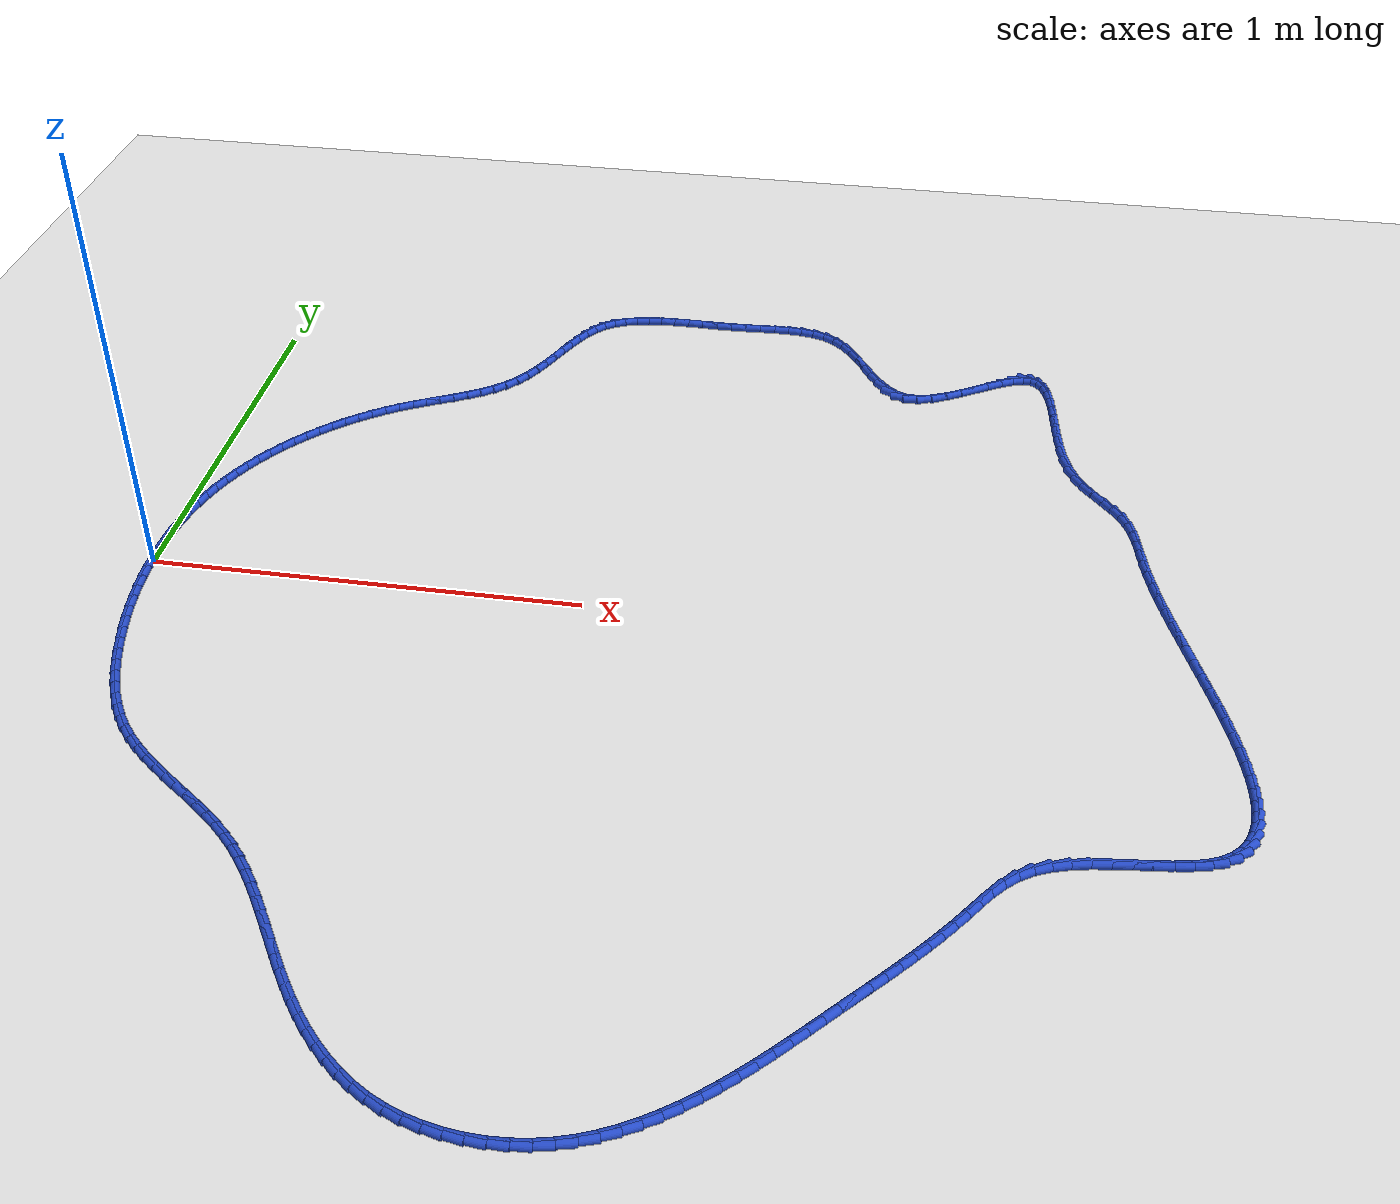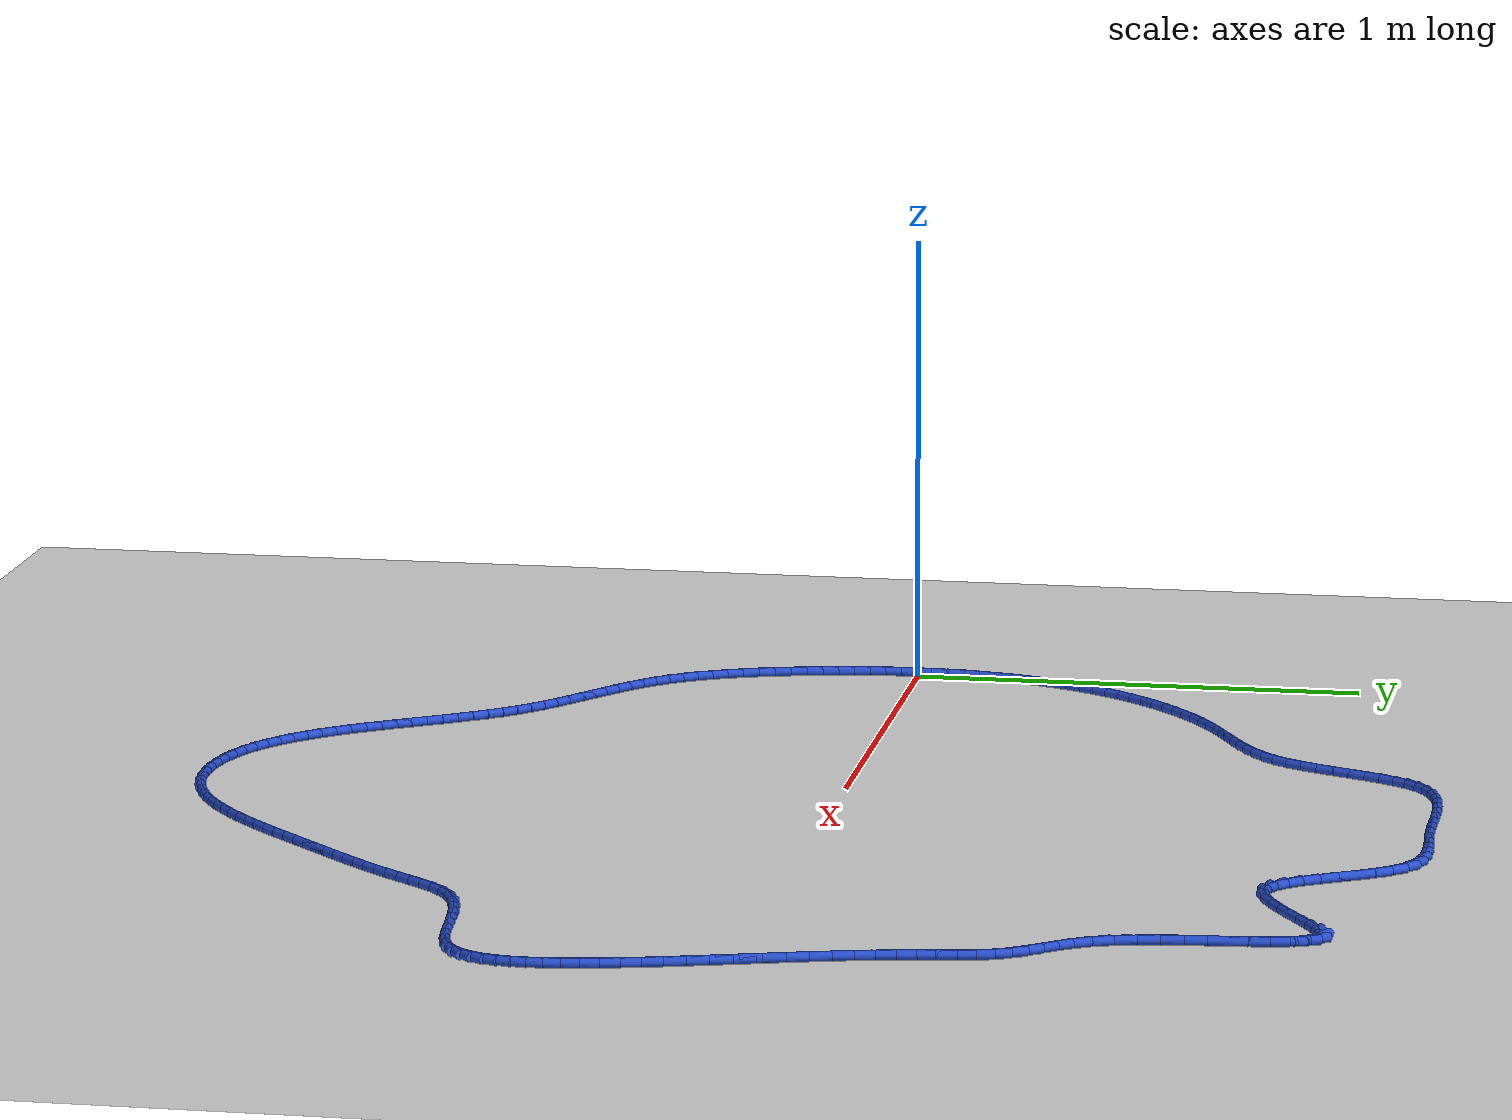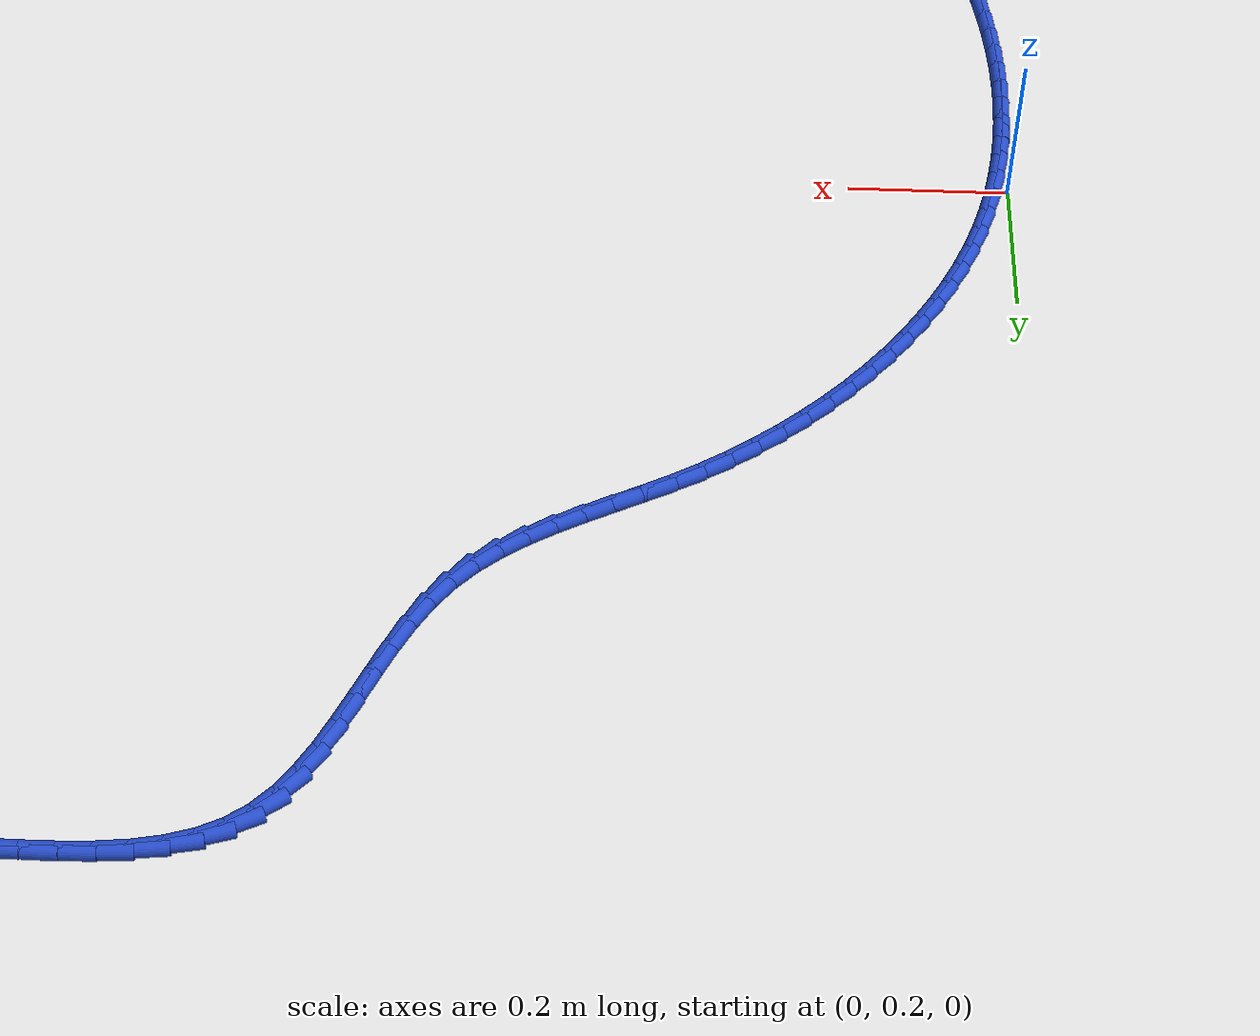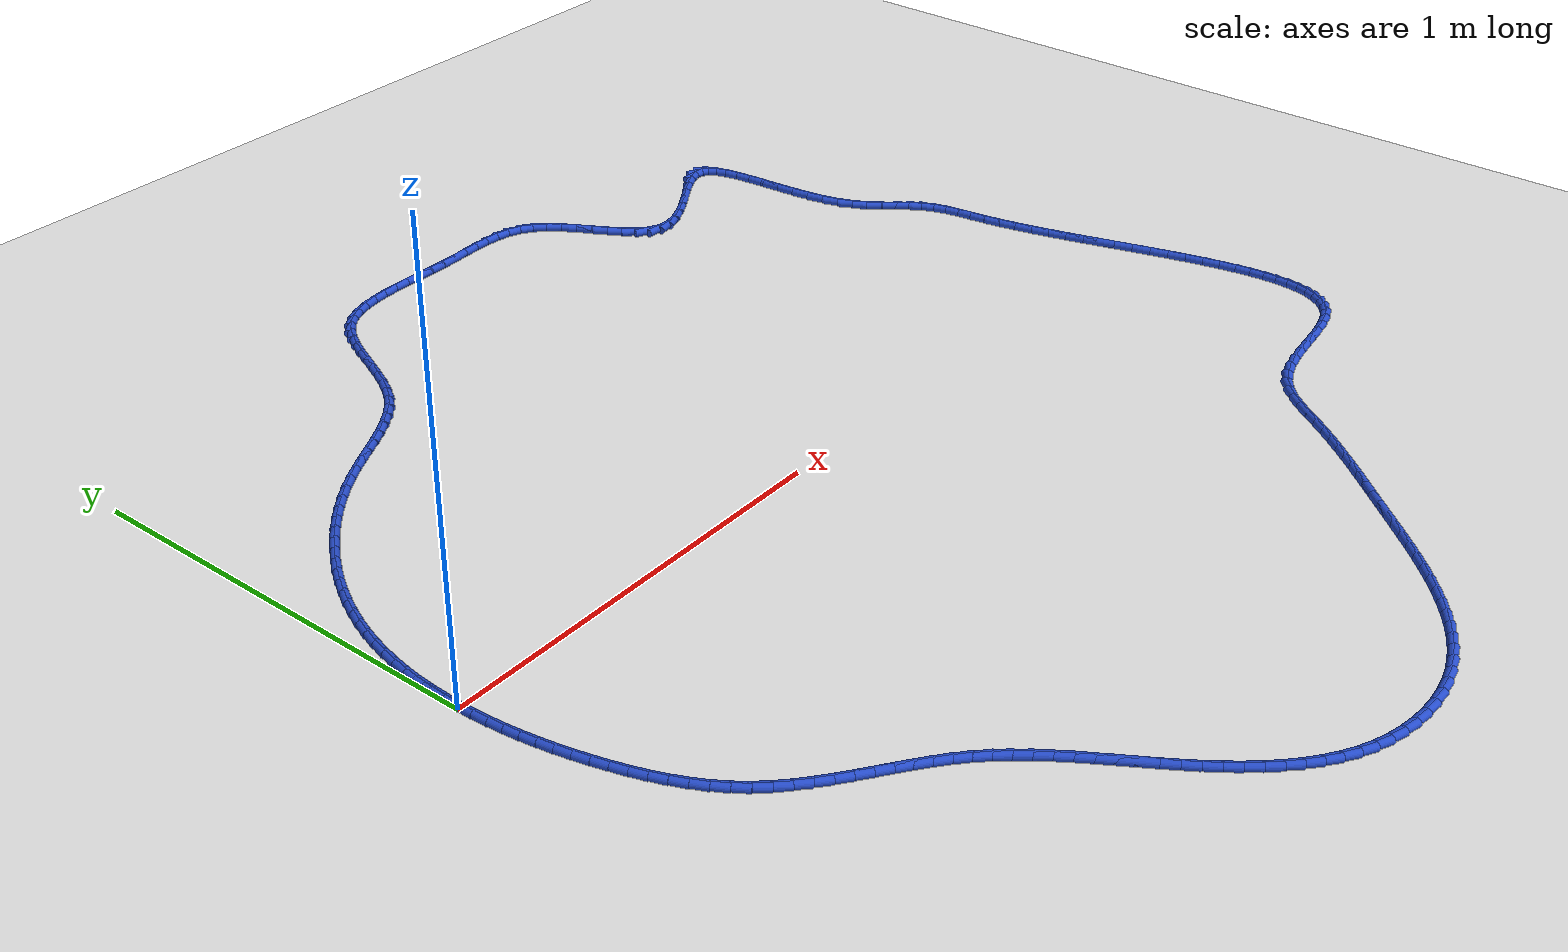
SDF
<sdf version="1.6">
 <world name="default">
  <light name="sun" type="directional">
   <pose>0 0 10 0 -0 0</pose>
   <diffuse>0.8 0.8 0.8 1</diffuse>
   <specular>0.2 0.2 0.2 1</specular>
   <attenuation>
    <range>1000</range>
    <constant>0.9</constant>
    <linear>0.01</linear>
    <quadratic>0.001</quadratic>
   </attenuation>
   <direction>-0.5 0.1 -0.9</direction>
  </light>
  <model name="ground_plane">
   <static>1</static>
   <link name="link">
    <collision name="collision">
     <geometry><plane><normal>0 0 1</normal><size>100 100</size></plane></geometry>
     <surface><friction><ode><mu>100</mu><mu2>50</mu2></ode></friction></surface>
    </collision>
    <visual name="visual">
     <cast_shadows>0</cast_shadows>
     <geometry><plane><normal>0 0 1</normal><size>100 100</size></plane></geometry>
     <material>
      <script><uri>file://media/materials/scripts/gazebo.material</uri><name>Gazebo/WhiteGlow</name></script>
     </material>
    </visual>
   </link>
  </model>
  <gravity>0 0 -9.8</gravity>
  <magnetic_field>6e-06 2.3e-05 -4.2e-05</magnetic_field>
  <atmosphere type="adiabatic"/>
  <physics name="default_physics" default="0" type="ode">
   <max_step_size>0.001</max_step_size>
   <real_time_factor>1</real_time_factor>
   <real_time_update_rate>1000</real_time_update_rate>
  </physics>
  <scene><ambient>0.4 0.4 0.4 1</ambient><background>0.7 0.7 0.7 1</background><shadows>1</shadows></scene>
  <spherical_coordinates>
   <surface_model>EARTH_WGS84</surface_model>
   <latitude_deg>0</latitude_deg>
   <longitude_deg>0</longitude_deg>
   <elevation>0</elevation>
   <heading_deg>0</heading_deg>
  </spherical_coordinates>
  <model name="line">
   <link name="link_0">
    <pose>2.0816681711721685e-17 2.7755575615628914e-17 0.01 0 1.57 1.5674172207228398</pose>
    <collision name="collision">
     <geometry><cylinder><radius>0.01</radius><length>0.08</length></cylinder></geometry>
    </collision>
    <visual name="visual">
     <material>
      <script><name>Gazebo/Blue</name><uri>file://media/materials/scripts/gazebo.material</uri></script>
     </material>
     <geometry><cylinder><radius>0.01</radius><length>0.08</length></cylinder></geometry>
    </visual>
   </link>
   <link name="link_1">
    <pose>0.00012144590236197738 0.03594010887325938 0.01 0 1.57 1.5309326183171914</pose>
    <collision name="collision">
     <geometry><cylinder><radius>0.01</radius><length>0.08</length></cylinder></geometry>
    </collision>
    <visual name="visual">
     <material>
      <script><name>Gazebo/Blue</name><uri>file://media/materials/scripts/gazebo.material</uri></script>
     </material>
     <geometry><cylinder><radius>0.01</radius><length>0.08</length></cylinder></geometry>
    </visual>
   </link>
   <link name="link_2">
    <pose>0.0015566333333428928 0.07192339239421906 0.01 0 1.57 1.4927208288331493</pose>
    <collision name="collision">
     <geometry><cylinder><radius>0.01</radius><length>0.08</length></cylinder></geometry>
    </collision>
    <visual name="visual">
     <material>
      <script><name>Gazebo/Blue</name><uri>file://media/materials/scripts/gazebo.material</uri></script>
     </material>
     <geometry><cylinder><radius>0.01</radius><length>0.08</length></cylinder></geometry>
    </visual>
   </link>
   <link name="link_3">
    <pose>0.004368637798115889 0.10786665788281713 0.01 0 1.57 1.4526475874665907</pose>
    <collision name="collision">
     <geometry><cylinder><radius>0.01</radius><length>0.08</length></cylinder></geometry>
    </collision>
    <visual name="visual">
     <material>
      <script><name>Gazebo/Blue</name><uri>file://media/materials/scripts/gazebo.material</uri></script>
     </material>
     <geometry><cylinder><radius>0.01</radius><length>0.08</length></cylinder></geometry>
    </visual>
   </link>
   <link name="link_4">
    <pose>0.008620534801854101 0.1436867126589916 0.01 0 1.57 1.4105896299389509</pose>
    <collision name="collision">
     <geometry><cylinder><radius>0.01</radius><length>0.08</length></cylinder></geometry>
    </collision>
    <visual name="visual">
     <material>
      <script><name>Gazebo/Blue</name><uri>file://media/materials/scripts/gazebo.material</uri></script>
     </material>
     <geometry><cylinder><radius>0.01</radius><length>0.08</length></cylinder></geometry>
    </visual>
   </link>
   <link name="link_5">
    <pose>0.014375399849730656 0.17930036404268065 0.01 0 1.57 1.3664394820661452</pose>
    <collision name="collision">
     <geometry><cylinder><radius>0.01</radius><length>0.08</length></cylinder></geometry>
    </collision>
    <visual name="visual">
     <material>
      <script><name>Gazebo/Blue</name><uri>file://media/materials/scripts/gazebo.material</uri></script>
     </material>
     <geometry><cylinder><radius>0.01</radius><length>0.08</length></cylinder></geometry>
    </visual>
   </link>
   <link name="link_6">
    <pose>0.021696308446918666 0.21462441935382215 0.01 0 1.57 1.3201114064045705</pose>
    <collision name="collision">
     <geometry><cylinder><radius>0.01</radius><length>0.08</length></cylinder></geometry>
    </collision>
    <visual name="visual">
     <material>
      <script><name>Gazebo/Blue</name><uri>file://media/materials/scripts/gazebo.material</uri></script>
     </material>
     <geometry><cylinder><radius>0.01</radius><length>0.08</length></cylinder></geometry>
    </visual>
   </link>
   <link name="link_7">
    <pose>0.03064633609859127 0.24957568591235416 0.01 0 1.57 1.2715486068925075</pose>
    <collision name="collision">
     <geometry><cylinder><radius>0.01</radius><length>0.08</length></cylinder></geometry>
    </collision>
    <visual name="visual">
     <material>
      <script><name>Gazebo/Blue</name><uri>file://media/materials/scripts/gazebo.material</uri></script>
     </material>
     <geometry><cylinder><radius>0.01</radius><length>0.08</length></cylinder></geometry>
    </visual>
   </link>
   <link name="link_8">
    <pose>0.04128855198792121 0.28407097234937434 0.01 0 1.57 1.221407493084309</pose>
    <collision name="collision">
     <geometry><cylinder><radius>0.01</radius><length>0.08</length></cylinder></geometry>
    </collision>
    <visual name="visual">
     <material>
      <script><name>Gazebo/Blue</name><uri>file://media/materials/scripts/gazebo.material</uri></script>
     </material>
     <geometry><cylinder><radius>0.01</radius><length>0.08</length></cylinder></geometry>
    </visual>
   </link>
   <link name="link_9">
    <pose>0.05366181786023806 0.3180321078287624 0.01 0 1.57 1.1718742541163207</pose>
    <collision name="collision">
     <geometry><cylinder><radius>0.01</radius><length>0.08</length></cylinder></geometry>
    </collision>
    <visual name="visual">
     <material>
      <script><name>Gazebo/Blue</name><uri>file://media/materials/scripts/gazebo.material</uri></script>
     </material>
     <geometry><cylinder><radius>0.01</radius><length>0.08</length></cylinder></geometry>
    </visual>
   </link>
   <link name="link_10">
    <pose>0.06772602024596482 0.3513973006809181 0.01 0 1.57 1.1233318672756718</pose>
    <collision name="collision">
     <geometry><cylinder><radius>0.01</radius><length>0.08</length></cylinder></geometry>
    </collision>
    <visual name="visual">
     <material>
      <script><name>Gazebo/Blue</name><uri>file://media/materials/scripts/gazebo.material</uri></script>
     </material>
     <geometry><cylinder><radius>0.01</radius><length>0.08</length></cylinder></geometry>
    </visual>
   </link>
   <link name="link_11">
    <pose>0.08342496671793496 0.38410809395238116 0.01 0 1.57 1.0756966413920814</pose>
    <collision name="collision">
     <geometry><cylinder><radius>0.01</radius><length>0.08</length></cylinder></geometry>
    </collision>
    <visual name="visual">
     <material>
      <script><name>Gazebo/Blue</name><uri>file://media/materials/scripts/gazebo.material</uri></script>
     </material>
     <geometry><cylinder><radius>0.01</radius><length>0.08</length></cylinder></geometry>
    </visual>
   </link>
   <link name="link_12">
    <pose>0.10070246484898222 0.41610603068969154 0.01 0 1.57 1.0288739197116965</pose>
    <collision name="collision">
     <geometry><cylinder><radius>0.01</radius><length>0.08</length></cylinder></geometry>
    </collision>
    <visual name="visual">
     <material>
      <script><name>Gazebo/Blue</name><uri>file://media/materials/scripts/gazebo.material</uri></script>
     </material>
     <geometry><cylinder><radius>0.01</radius><length>0.08</length></cylinder></geometry>
    </visual>
   </link>
   <link name="link_13">
    <pose>0.11950232221194006 0.4473326539393886 0.01 0 1.57 0.9827605711106946</pose>
    <collision name="collision">
     <geometry><cylinder><radius>0.01</radius><length>0.08</length></cylinder></geometry>
    </collision>
    <visual name="visual">
     <material>
      <script><name>Gazebo/Blue</name><uri>file://media/materials/scripts/gazebo.material</uri></script>
     </material>
     <geometry><cylinder><radius>0.01</radius><length>0.08</length></cylinder></geometry>
    </visual>
   </link>
   <link name="link_14">
    <pose>0.13976834637964208 0.47772950674801223 0.01 0 1.57 0.9372471302772714</pose>
    <collision name="collision">
     <geometry><cylinder><radius>0.01</radius><length>0.08</length></cylinder></geometry>
    </collision>
    <visual name="visual">
     <material>
      <script><name>Gazebo/Blue</name><uri>file://media/materials/scripts/gazebo.material</uri></script>
     </material>
     <geometry><cylinder><radius>0.01</radius><length>0.08</length></cylinder></geometry>
    </visual>
   </link>
   <link name="link_15">
    <pose>0.16144434492492196 0.5072381321621023 0.01 0 1.57 0.8922196109677276</pose>
    <collision name="collision">
     <geometry><cylinder><radius>0.01</radius><length>0.08</length></cylinder></geometry>
    </collision>
    <visual name="visual">
     <material>
      <script><name>Gazebo/Blue</name><uri>file://media/materials/scripts/gazebo.material</uri></script>
     </material>
     <geometry><cylinder><radius>0.01</radius><length>0.08</length></cylinder></geometry>
    </visual>
   </link>
   <link name="link_16">
    <pose>0.18447412542061323 0.5358000732281987 0.01 0 1.57 0.8475610339252838</pose>
    <collision name="collision">
     <geometry><cylinder><radius>0.01</radius><length>0.08</length></cylinder></geometry>
    </collision>
    <visual name="visual">
     <material>
      <script><name>Gazebo/Blue</name><uri>file://media/materials/scripts/gazebo.material</uri></script>
     </material>
     <geometry><cylinder><radius>0.01</radius><length>0.08</length></cylinder></geometry>
    </visual>
   </link>
   <link name="link_17">
    <pose>0.20880149543954943 0.5633568729928409 0.01 0 1.57 0.8031527217122393</pose>
    <collision name="collision">
     <geometry><cylinder><radius>0.01</radius><length>0.08</length></cylinder></geometry>
    </collision>
    <visual name="visual">
     <material>
      <script><name>Gazebo/Blue</name><uri>file://media/materials/scripts/gazebo.material</uri></script>
     </material>
     <geometry><cylinder><radius>0.01</radius><length>0.08</length></cylinder></geometry>
    </visual>
   </link>
   <link name="link_18">
    <pose>0.23437026255456422 0.5898500745025688 0.01 0 1.57 0.7588754183974462</pose>
    <collision name="collision">
     <geometry><cylinder><radius>0.01</radius><length>0.08</length></cylinder></geometry>
    </collision>
    <visual name="visual">
     <material>
      <script><name>Gazebo/Blue</name><uri>file://media/materials/scripts/gazebo.material</uri></script>
     </material>
     <geometry><cylinder><radius>0.01</radius><length>0.08</length></cylinder></geometry>
    </visual>
   </link>
   <link name="link_19">
    <pose>0.2611242343384911 0.6152212208039219 0.01 0 1.57 0.7146102943155618</pose>
    <collision name="collision">
     <geometry><cylinder><radius>0.01</radius><length>0.08</length></cylinder></geometry>
    </collision>
    <visual name="visual">
     <material>
      <script><name>Gazebo/Blue</name><uri>file://media/materials/scripts/gazebo.material</uri></script>
     </material>
     <geometry><cylinder><radius>0.01</radius><length>0.08</length></cylinder></geometry>
    </visual>
   </link>
   <link name="link_20">
    <pose>0.28900721836416365 0.6394118549434401 0.01 0 1.57 0.6702398961260468</pose>
    <collision name="collision">
     <geometry><cylinder><radius>0.01</radius><length>0.08</length></cylinder></geometry>
    </collision>
    <visual name="visual">
     <material>
      <script><name>Gazebo/Blue</name><uri>file://media/materials/scripts/gazebo.material</uri></script>
     </material>
     <geometry><cylinder><radius>0.01</radius><length>0.08</length></cylinder></geometry>
    </visual>
   </link>
   <link name="link_21">
    <pose>0.31796302220441547 0.6623635199676632 0.01 0 1.57 0.6256491008757675</pose>
    <collision name="collision">
     <geometry><cylinder><radius>0.01</radius><length>0.08</length></cylinder></geometry>
    </collision>
    <visual name="visual">
     <material>
      <script><name>Gazebo/Blue</name><uri>file://media/materials/scripts/gazebo.material</uri></script>
     </material>
     <geometry><cylinder><radius>0.01</radius><length>0.08</length></cylinder></geometry>
    </visual>
   </link>
   <link name="link_22">
    <pose>0.3479354534320803 0.6840177589231312 0.01 0 1.57 0.5807261300224197</pose>
    <collision name="collision">
     <geometry><cylinder><radius>0.01</radius><length>0.08</length></cylinder></geometry>
    </collision>
    <visual name="visual">
     <material>
      <script><name>Gazebo/Blue</name><uri>file://media/materials/scripts/gazebo.material</uri></script>
     </material>
     <geometry><cylinder><radius>0.01</radius><length>0.08</length></cylinder></geometry>
    </visual>
   </link>
   <link name="link_23">
    <pose>0.37886831961999157 0.7043161148563835 0.01 0 1.57 0.535577071561149</pose>
    <collision name="collision">
     <geometry><cylinder><radius>0.01</radius><length>0.08</length></cylinder></geometry>
    </collision>
    <visual name="visual">
     <material>
      <script><name>Gazebo/Blue</name><uri>file://media/materials/scripts/gazebo.material</uri></script>
     </material>
     <geometry><cylinder><radius>0.01</radius><length>0.08</length></cylinder></geometry>
    </visual>
   </link>
   <link name="link_24">
    <pose>0.410701189025113 0.7232068003860688 0.01 0 1.57 0.49868385476483523</pose>
    <collision name="collision">
     <geometry><cylinder><radius>0.01</radius><length>0.08</length></cylinder></geometry>
    </collision>
    <visual name="visual">
     <material>
      <script><name>Gazebo/Blue</name><uri>file://media/materials/scripts/gazebo.material</uri></script>
     </material>
     <geometry><cylinder><radius>0.01</radius><length>0.08</length></cylinder></geometry>
    </visual>
   </link>
   <link name="link_25">
    <pose>0.44320269669220885 0.7409069515655644 0.01 0 1.57 0.481225126800873</pose>
    <collision name="collision">
     <geometry><cylinder><radius>0.01</radius><length>0.08</length></cylinder></geometry>
    </collision>
    <visual name="visual">
     <material>
      <script><name>Gazebo/Blue</name><uri>file://media/materials/scripts/gazebo.material</uri></script>
     </material>
     <geometry><cylinder><radius>0.01</radius><length>0.08</length></cylinder></geometry>
    </visual>
   </link>
   <link name="link_26">
    <pose>0.4759158166371641 0.7579887293038019 0.01 0 1.57 0.4839888741750512</pose>
    <collision name="collision">
     <geometry><cylinder><radius>0.01</radius><length>0.08</length></cylinder></geometry>
    </collision>
    <visual name="visual">
     <material>
      <script><name>Gazebo/Blue</name><uri>file://media/materials/scripts/gazebo.material</uri></script>
     </material>
     <geometry><cylinder><radius>0.01</radius><length>0.08</length></cylinder></geometry>
    </visual>
   </link>
   <link name="link_27">
    <pose>0.5083680725927255 0.775048601917006 0.01 0 1.57 0.5074072052652896</pose>
    <collision name="collision">
     <geometry><cylinder><radius>0.01</radius><length>0.08</length></cylinder></geometry>
    </collision>
    <visual name="visual">
     <material>
      <script><name>Gazebo/Blue</name><uri>file://media/materials/scripts/gazebo.material</uri></script>
     </material>
     <geometry><cylinder><radius>0.01</radius><length>0.08</length></cylinder></geometry>
    </visual>
   </link>
   <link name="link_28">
    <pose>0.5400869882916401 0.7926830377214015 0.01 0 1.57 0.5523244619791184</pose>
    <collision name="collision">
     <geometry><cylinder><radius>0.01</radius><length>0.08</length></cylinder></geometry>
    </collision>
    <visual name="visual">
     <material>
      <script><name>Gazebo/Blue</name><uri>file://media/materials/scripts/gazebo.material</uri></script>
     </material>
     <geometry><cylinder><radius>0.01</radius><length>0.08</length></cylinder></geometry>
    </visual>
   </link>
   <link name="link_29">
    <pose>0.5706000874666554 0.8114885050332135 0.01 0 1.57 0.6197136887666675</pose>
    <collision name="collision">
     <geometry><cylinder><radius>0.01</radius><length>0.08</length></cylinder></geometry>
    </collision>
    <visual name="visual">
     <material>
      <script><name>Gazebo/Blue</name><uri>file://media/materials/scripts/gazebo.material</uri></script>
     </material>
     <geometry><cylinder><radius>0.01</radius><length>0.08</length></cylinder></geometry>
    </visual>
   </link>
   <link name="link_30">
    <pose>0.5994348938505183 0.8320614721686669 0.01 0 1.57 0.7100267309773654</pose>
    <collision name="collision">
     <geometry><cylinder><radius>0.01</radius><length>0.08</length></cylinder></geometry>
    </collision>
    <visual name="visual">
     <material>
      <script><name>Gazebo/Blue</name><uri>file://media/materials/scripts/gazebo.material</uri></script>
     </material>
     <geometry><cylinder><radius>0.01</radius><length>0.08</length></cylinder></geometry>
    </visual>
   </link>
   <link name="link_31">
    <pose>0.6261189311759756 0.8549984074439864 0.01 0 1.57 0.8221439703588708</pose>
    <collision name="collision">
     <geometry><cylinder><radius>0.01</radius><length>0.08</length></cylinder></geometry>
    </collision>
    <visual name="visual">
     <material>
      <script><name>Gazebo/Blue</name><uri>file://media/materials/scripts/gazebo.material</uri></script>
     </material>
     <geometry><cylinder><radius>0.01</radius><length>0.08</length></cylinder></geometry>
    </visual>
   </link>
   <link name="link_32">
    <pose>0.6501797231757748 0.8808957791753966 0.01 0 1.57 0.9450977270257772</pose>
    <collision name="collision">
     <geometry><cylinder><radius>0.01</radius><length>0.08</length></cylinder></geometry>
    </collision>
    <visual name="visual">
     <material>
      <script><name>Gazebo/Blue</name><uri>file://media/materials/scripts/gazebo.material</uri></script>
     </material>
     <geometry><cylinder><radius>0.01</radius><length>0.08</length></cylinder></geometry>
    </visual>
   </link>
   <link name="link_33">
    <pose>0.6713083735792571 0.9101376745909182 0.01 0 1.57 1.0437798711639306</pose>
    <collision name="collision">
     <geometry><cylinder><radius>0.01</radius><length>0.08</length></cylinder></geometry>
    </collision>
    <visual name="visual">
     <material>
      <script><name>Gazebo/Blue</name><uri>file://media/materials/scripts/gazebo.material</uri></script>
     </material>
     <geometry><cylinder><radius>0.01</radius><length>0.08</length></cylinder></geometry>
    </visual>
   </link>
   <link name="link_34">
    <pose>0.6899356297273433 0.9421478782019689 0.01 0 1.57 1.1118739134698177</pose>
    <collision name="collision">
     <geometry><cylinder><radius>0.01</radius><length>0.08</length></cylinder></geometry>
    </collision>
    <visual name="visual">
     <material>
      <script><name>Gazebo/Blue</name><uri>file://media/materials/scripts/gazebo.material</uri></script>
     </material>
     <geometry><cylinder><radius>0.01</radius><length>0.08</length></cylinder></geometry>
    </visual>
   </link>
   <link name="link_35">
    <pose>0.7067011909677737 0.9760788855145004 0.01 0 1.57 1.1529032584751293</pose>
    <collision name="collision">
     <geometry><cylinder><radius>0.01</radius><length>0.08</length></cylinder></geometry>
    </collision>
    <visual name="visual">
     <material>
      <script><name>Gazebo/Blue</name><uri>file://media/materials/scripts/gazebo.material</uri></script>
     </material>
     <geometry><cylinder><radius>0.01</radius><length>0.08</length></cylinder></geometry>
    </visual>
   </link>
   <link name="link_36">
    <pose>0.7222447692543656 1.0110831756675907 0.01 0 1.57 1.1692013526739744</pose>
    <collision name="collision">
     <geometry><cylinder><radius>0.01</radius><length>0.08</length></cylinder></geometry>
    </collision>
    <visual name="visual">
     <material>
      <script><name>Gazebo/Blue</name><uri>file://media/materials/scripts/gazebo.material</uri></script>
     </material>
     <geometry><cylinder><radius>0.01</radius><length>0.08</length></cylinder></geometry>
    </visual>
   </link>
   <link name="link_37">
    <pose>0.7372060765409374 1.0463132278003195 0.01 0 1.57 1.1613577813072005</pose>
    <collision name="collision">
     <geometry><cylinder><radius>0.01</radius><length>0.08</length></cylinder></geometry>
    </collision>
    <visual name="visual">
     <material>
      <script><name>Gazebo/Blue</name><uri>file://media/materials/scripts/gazebo.material</uri></script>
     </material>
     <geometry><cylinder><radius>0.01</radius><length>0.08</length></cylinder></geometry>
    </visual>
   </link>
   <link name="link_38">
    <pose>0.7522248247813071 1.0809215210517662 0.01 0 1.57 1.1279669004457198</pose>
    <collision name="collision">
     <geometry><cylinder><radius>0.01</radius><length>0.08</length></cylinder></geometry>
    </collision>
    <visual name="visual">
     <material>
      <script><name>Gazebo/Blue</name><uri>file://media/materials/scripts/gazebo.material</uri></script>
     </material>
     <geometry><cylinder><radius>0.01</radius><length>0.08</length></cylinder></geometry>
    </visual>
   </link>
   <link name="link_39">
    <pose>0.767940725929293 1.1140605345610102 0.01 0 1.57 1.0654519811790344</pose>
    <collision name="collision">
     <geometry><cylinder><radius>0.01</radius><length>0.08</length></cylinder></geometry>
    </collision>
    <visual name="visual">
     <material>
      <script><name>Gazebo/Blue</name><uri>file://media/materials/scripts/gazebo.material</uri></script>
     </material>
     <geometry><cylinder><radius>0.01</radius><length>0.08</length></cylinder></geometry>
    </visual>
   </link>
   <link name="link_40">
    <pose>0.7849934919387125 1.1448827474671301 0.01 0 1.57 0.9681520278842968</pose>
    <collision name="collision">
     <geometry><cylinder><radius>0.01</radius><length>0.08</length></cylinder></geometry>
    </collision>
    <visual name="visual">
     <material>
      <script><name>Gazebo/Blue</name><uri>file://media/materials/scripts/gazebo.material</uri></script>
     </material>
     <geometry><cylinder><radius>0.01</radius><length>0.08</length></cylinder></geometry>
    </visual>
   </link>
   <link name="link_41">
    <pose>0.804022834763384 1.1725406389092055 0.01 0 1.57 0.8295369154258269</pose>
    <collision name="collision">
     <geometry><cylinder><radius>0.01</radius><length>0.08</length></cylinder></geometry>
    </collision>
    <visual name="visual">
     <material>
      <script><name>Gazebo/Blue</name><uri>file://media/materials/scripts/gazebo.material</uri></script>
     </material>
     <geometry><cylinder><radius>0.01</radius><length>0.08</length></cylinder></geometry>
    </visual>
   </link>
   <link name="link_42">
    <pose>0.8256684663571259 1.1961866880263161 0.01 0 1.57 0.6493707266785183</pose>
    <collision name="collision">
     <geometry><cylinder><radius>0.01</radius><length>0.08</length></cylinder></geometry>
    </collision>
    <visual name="visual">
     <material>
      <script><name>Gazebo/Blue</name><uri>file://media/materials/scripts/gazebo.material</uri></script>
     </material>
     <geometry><cylinder><radius>0.01</radius><length>0.08</length></cylinder></geometry>
    </visual>
   </link>
   <link name="link_43">
    <pose>0.8505169869506801 1.21505198146899 0.01 0 1.57 0.46808149278677075</pose>
    <collision name="collision">
     <geometry><cylinder><radius>0.01</radius><length>0.08</length></cylinder></geometry>
    </collision>
    <visual name="visual">
     <material>
      <script><name>Gazebo/Blue</name><uri>file://media/materials/scripts/gazebo.material</uri></script>
     </material>
     <geometry><cylinder><radius>0.01</radius><length>0.08</length></cylinder></geometry>
    </visual>
   </link>
   <link name="link_44">
    <pose>0.8785695521231768 1.2292340877958894 0.01 0 1.57 0.31695342697430634</pose>
    <collision name="collision">
     <geometry><cylinder><radius>0.01</radius><length>0.08</length></cylinder></geometry>
    </collision>
    <visual name="visual">
     <material>
      <script><name>Gazebo/Blue</name><uri>file://media/materials/scripts/gazebo.material</uri></script>
     </material>
     <geometry><cylinder><radius>0.01</radius><length>0.08</length></cylinder></geometry>
    </visual>
   </link>
   <link name="link_45">
    <pose>0.9094642617387013 1.2393679127979207 0.01 0 1.57 0.19896759945817444</pose>
    <collision name="collision">
     <geometry><cylinder><radius>0.01</radius><length>0.08</length></cylinder></geometry>
    </collision>
    <visual name="visual">
     <material>
      <script><name>Gazebo/Blue</name><uri>file://media/materials/scripts/gazebo.material</uri></script>
     </material>
     <geometry><cylinder><radius>0.01</radius><length>0.08</length></cylinder></geometry>
    </visual>
   </link>
   <link name="link_46">
    <pose>0.9428337901564282 1.2460963922340405 0.01 0 1.57 0.11133038069278822</pose>
    <collision name="collision">
     <geometry><cylinder><radius>0.01</radius><length>0.08</length></cylinder></geometry>
    </collision>
    <visual name="visual">
     <material>
      <script><name>Gazebo/Blue</name><uri>file://media/materials/scripts/gazebo.material</uri></script>
     </material>
     <geometry><cylinder><radius>0.01</radius><length>0.08</length></cylinder></geometry>
    </visual>
   </link>
   <link name="link_47">
    <pose>0.9783108117355317 1.2500624618632068 0.01 0 1.57 0.049576083820147436</pose>
    <collision name="collision">
     <geometry><cylinder><radius>0.01</radius><length>0.08</length></cylinder></geometry>
    </collision>
    <visual name="visual">
     <material>
      <script><name>Gazebo/Blue</name><uri>file://media/materials/scripts/gazebo.material</uri></script>
     </material>
     <geometry><cylinder><radius>0.01</radius><length>0.08</length></cylinder></geometry>
    </visual>
   </link>
   <link name="link_48">
    <pose>1.015528000835186 1.251909057444377 0.01 0 1.57 0.009589159173276</pose>
    <collision name="collision">
     <geometry><cylinder><radius>0.01</radius><length>0.08</length></cylinder></geometry>
    </collision>
    <visual name="visual">
     <material>
      <script><name>Gazebo/Blue</name><uri>file://media/materials/scripts/gazebo.material</uri></script>
     </material>
     <geometry><cylinder><radius>0.01</radius><length>0.08</length></cylinder></geometry>
    </visual>
   </link>
   <link name="link_49">
    <pose>1.054118031814565 1.2522791147365089 0.01 0 1.57 -0.011706469422779921</pose>
    <collision name="collision">
     <geometry><cylinder><radius>0.01</radius><length>0.08</length></cylinder></geometry>
    </collision>
    <visual name="visual">
     <material>
      <script><name>Gazebo/Blue</name><uri>file://media/materials/scripts/gazebo.material</uri></script>
     </material>
     <geometry><cylinder><radius>0.01</radius><length>0.08</length></cylinder></geometry>
    </visual>
   </link>
   <link name="link_50">
    <pose>1.0937135790328436 1.2518155694985595 0.01 0 1.57 -0.016258851315477024</pose>
    <collision name="collision">
     <geometry><cylinder><radius>0.01</radius><length>0.08</length></cylinder></geometry>
    </collision>
    <visual name="visual">
     <material>
      <script><name>Gazebo/Blue</name><uri>file://media/materials/scripts/gazebo.material</uri></script>
     </material>
     <geometry><cylinder><radius>0.01</radius><length>0.08</length></cylinder></geometry>
    </visual>
   </link>
   <link name="link_51">
    <pose>1.133947316849196 1.2511613574894864 0.01 0 1.57 -0.004985639512612113</pose>
    <collision name="collision">
     <geometry><cylinder><radius>0.01</radius><length>0.08</length></cylinder></geometry>
    </collision>
    <visual name="visual">
     <material>
      <script><name>Gazebo/Blue</name><uri>file://media/materials/scripts/gazebo.material</uri></script>
     </material>
     <geometry><cylinder><radius>0.01</radius><length>0.08</length></cylinder></geometry>
    </visual>
   </link>
   <link name="link_52">
    <pose>1.1744519196227958 1.2509594144682472 0.01 0 1.57 0.02177195839776627</pose>
    <collision name="collision">
     <geometry><cylinder><radius>0.01</radius><length>0.08</length></cylinder></geometry>
    </collision>
    <visual name="visual">
     <material>
      <script><name>Gazebo/Blue</name><uri>file://media/materials/scripts/gazebo.material</uri></script>
     </material>
     <geometry><cylinder><radius>0.01</radius><length>0.08</length></cylinder></geometry>
    </visual>
   </link>
   <link name="link_53">
    <pose>1.2148598769473091 1.251839313867884 0.01 0 1.57 0.046858813639401704</pose>
    <collision name="collision">
     <geometry><cylinder><radius>0.01</radius><length>0.08</length></cylinder></geometry>
    </collision>
    <visual name="visual">
     <material>
      <script><name>Gazebo/Blue</name><uri>file://media/materials/scripts/gazebo.material</uri></script>
     </material>
     <geometry><cylinder><radius>0.01</radius><length>0.08</length></cylinder></geometry>
    </visual>
   </link>
   <link name="link_54">
    <pose>1.2547937408275065 1.2537119381579622 0.01 0 1.57 0.04368002936239693</pose>
    <collision name="collision">
     <geometry><cylinder><radius>0.01</radius><length>0.08</length></cylinder></geometry>
    </collision>
    <visual name="visual">
     <material>
      <script><name>Gazebo/Blue</name><uri>file://media/materials/scripts/gazebo.material</uri></script>
     </material>
     <geometry><cylinder><radius>0.01</radius><length>0.08</length></cylinder></geometry>
    </visual>
   </link>
   <link name="link_55">
    <pose>1.293861286342573 1.2554194958066738 0.01 0 1.57 0.007878321877856217</pose>
    <collision name="collision">
     <geometry><cylinder><radius>0.01</radius><length>0.08</length></cylinder></geometry>
    </collision>
    <visual name="visual">
     <material>
      <script><name>Gazebo/Blue</name><uri>file://media/materials/scripts/gazebo.material</uri></script>
     </material>
     <geometry><cylinder><radius>0.01</radius><length>0.08</length></cylinder></geometry>
    </visual>
   </link>
   <link name="link_56">
    <pose>1.3316690879254736 1.2557173639997534 0.01 0 1.57 -0.06508476731705301</pose>
    <collision name="collision">
     <geometry><cylinder><radius>0.01</radius><length>0.08</length></cylinder></geometry>
    </collision>
    <visual name="visual">
     <material>
      <script><name>Gazebo/Blue</name><uri>file://media/materials/scripts/gazebo.material</uri></script>
     </material>
     <geometry><cylinder><radius>0.01</radius><length>0.08</length></cylinder></geometry>
    </visual>
   </link>
   <link name="link_57">
    <pose>1.3678237200091734 1.253360919922937 0.01 0 1.57 -0.1813832845481044</pose>
    <collision name="collision">
     <geometry><cylinder><radius>0.01</radius><length>0.08</length></cylinder></geometry>
    </collision>
    <visual name="visual">
     <material>
      <script><name>Gazebo/Blue</name><uri>file://media/materials/scripts/gazebo.material</uri></script>
     </material>
     <geometry><cylinder><radius>0.01</radius><length>0.08</length></cylinder></geometry>
    </visual>
   </link>
   <link name="link_58">
    <pose>1.4019317570266374 1.2471055407619585 0.01 0 1.57 -0.34551228261787065</pose>
    <collision name="collision">
     <geometry><cylinder><radius>0.01</radius><length>0.08</length></cylinder></geometry>
    </collision>
    <visual name="visual">
     <material>
      <script><name>Gazebo/Blue</name><uri>file://media/materials/scripts/gazebo.material</uri></script>
     </material>
     <geometry><cylinder><radius>0.01</radius><length>0.08</length></cylinder></geometry>
    </visual>
   </link>
   <link name="link_59">
    <pose>1.4335997734108312 1.2357066037025533 0.01 0 1.57 -0.552730054115268</pose>
    <collision name="collision">
     <geometry><cylinder><radius>0.01</radius><length>0.08</length></cylinder></geometry>
    </collision>
    <visual name="visual">
     <material>
      <script><name>Gazebo/Blue</name><uri>file://media/materials/scripts/gazebo.material</uri></script>
     </material>
     <geometry><cylinder><radius>0.01</radius><length>0.08</length></cylinder></geometry>
    </visual>
   </link>
   <link name="link_60">
    <pose>1.4624343435947182 1.2179194859304563 0.01 0 1.57 -0.7675103519102068</pose>
    <collision name="collision">
     <geometry><cylinder><radius>0.01</radius><length>0.08</length></cylinder></geometry>
    </collision>
    <visual name="visual">
     <material>
      <script><name>Gazebo/Blue</name><uri>file://media/materials/scripts/gazebo.material</uri></script>
     </material>
     <geometry><cylinder><radius>0.01</radius><length>0.08</length></cylinder></geometry>
    </visual>
   </link>
   <link name="link_61">
    <pose>1.4882272885885828 1.193033178551508 0.01 0 1.57 -0.9184080681413549</pose>
    <collision name="collision">
     <geometry><cylinder><radius>0.01</radius><length>0.08</length></cylinder></geometry>
    </collision>
    <visual name="visual">
     <material>
      <script><name>Gazebo/Blue</name><uri>file://media/materials/scripts/gazebo.material</uri></script>
     </material>
     <geometry><cylinder><radius>0.01</radius><length>0.08</length></cylinder></geometry>
    </visual>
   </link>
   <link name="link_62">
    <pose>1.511531617426895 1.1625293206081948 0.01 0 1.57 -1.006597355352516</pose>
    <collision name="collision">
     <geometry><cylinder><radius>0.01</radius><length>0.08</length></cylinder></geometry>
    </collision>
    <visual name="visual">
     <material>
      <script><name>Gazebo/Blue</name><uri>file://media/materials/scripts/gazebo.material</uri></script>
     </material>
     <geometry><cylinder><radius>0.01</radius><length>0.08</length></cylinder></geometry>
    </visual>
   </link>
   <link name="link_63">
    <pose>1.5330958235110905 1.128452655632629 0.01 0 1.57 -1.04685684481578</pose>
    <collision name="collision">
     <geometry><cylinder><radius>0.01</radius><length>0.08</length></cylinder></geometry>
    </collision>
    <visual name="visual">
     <material>
      <script><name>Gazebo/Blue</name><uri>file://media/materials/scripts/gazebo.material</uri></script>
     </material>
     <geometry><cylinder><radius>0.01</radius><length>0.08</length></cylinder></geometry>
    </visual>
   </link>
   <link name="link_64">
    <pose>1.5536684003797665 1.0928479275520264 0.01 0 1.57 -1.0456738519528401</pose>
    <collision name="collision">
     <geometry><cylinder><radius>0.01</radius><length>0.08</length></cylinder></geometry>
    </collision>
    <visual name="visual">
     <material>
      <script><name>Gazebo/Blue</name><uri>file://media/materials/scripts/gazebo.material</uri></script>
     </material>
     <geometry><cylinder><radius>0.01</radius><length>0.08</length></cylinder></geometry>
    </visual>
   </link>
   <link name="link_65">
    <pose>1.5739978415715217 1.0577598802936028 0.01 0 1.57 -1.0010958635490124</pose>
    <collision name="collision">
     <geometry><cylinder><radius>0.01</radius><length>0.08</length></cylinder></geometry>
    </collision>
    <visual name="visual">
     <material>
      <script><name>Gazebo/Blue</name><uri>file://media/materials/scripts/gazebo.material</uri></script>
     </material>
     <geometry><cylinder><radius>0.01</radius><length>0.08</length></cylinder></geometry>
    </visual>
   </link>
   <link name="link_66">
    <pose>1.594832640624953 1.0252332577845722 0.01 0 1.57 -0.9014886530146303</pose>
    <collision name="collision">
     <geometry><cylinder><radius>0.01</radius><length>0.08</length></cylinder></geometry>
    </collision>
    <visual name="visual">
     <material>
      <script><name>Gazebo/Blue</name><uri>file://media/materials/scripts/gazebo.material</uri></script>
     </material>
     <geometry><cylinder><radius>0.01</radius><length>0.08</length></cylinder></geometry>
    </visual>
   </link>
   <link name="link_67">
    <pose>1.6169212910786575 0.9973128039521512 0.01 0 1.57 -0.7232775594969701</pose>
    <collision name="collision">
     <geometry><cylinder><radius>0.01</radius><length>0.08</length></cylinder></geometry>
    </collision>
    <visual name="visual">
     <material>
      <script><name>Gazebo/Blue</name><uri>file://media/materials/scripts/gazebo.material</uri></script>
     </material>
     <geometry><cylinder><radius>0.01</radius><length>0.08</length></cylinder></geometry>
    </visual>
   </link>
   <link name="link_68">
    <pose>1.6410122864712335 0.9760432627235544 0.01 0 1.57 -0.4380853083773497</pose>
    <collision name="collision">
     <geometry><cylinder><radius>0.01</radius><length>0.08</length></cylinder></geometry>
    </collision>
    <visual name="visual">
     <material>
      <script><name>Gazebo/Blue</name><uri>file://media/materials/scripts/gazebo.material</uri></script>
     </material>
     <geometry><cylinder><radius>0.01</radius><length>0.08</length></cylinder></geometry>
    </visual>
   </link>
   <link name="link_69">
    <pose>1.6678541203412771 0.9634693780259969 0.01 0 1.57 -0.06837614948621258</pose>
    <collision name="collision">
     <geometry><cylinder><radius>0.01</radius><length>0.08</length></cylinder></geometry>
    </collision>
    <visual name="visual">
     <material>
      <script><name>Gazebo/Blue</name><uri>file://media/materials/scripts/gazebo.material</uri></script>
     </material>
     <geometry><cylinder><radius>0.01</radius><length>0.08</length></cylinder></geometry>
    </visual>
   </link>
   <link name="link_70">
    <pose>1.6981020600475365 0.961397911130792 0.01 0 1.57 0.22588829474566882</pose>
    <collision name="collision">
     <geometry><cylinder><radius>0.01</radius><length>0.08</length></cylinder></geometry>
    </collision>
    <visual name="visual">
     <material>
      <script><name>Gazebo/Blue</name><uri>file://media/materials/scripts/gazebo.material</uri></script>
     </material>
     <geometry><cylinder><radius>0.01</radius><length>0.08</length></cylinder></geometry>
    </visual>
   </link>
   <link name="link_71">
    <pose>1.7313983974820142 0.9690497553446311 0.01 0 1.57 0.4013756108138547</pose>
    <collision name="collision">
     <geometry><cylinder><radius>0.01</radius><length>0.08</length></cylinder></geometry>
    </collision>
    <visual name="visual">
     <material>
      <script><name>Gazebo/Blue</name><uri>file://media/materials/scripts/gazebo.material</uri></script>
     </material>
     <geometry><cylinder><radius>0.01</radius><length>0.08</length></cylinder></geometry>
    </visual>
   </link>
   <link name="link_72">
    <pose>1.7667640026262244 0.9840594723565018 0.01 0 1.57 0.5014404017447036</pose>
    <collision name="collision">
     <geometry><cylinder><radius>0.01</radius><length>0.08</length></cylinder></geometry>
    </collision>
    <visual name="visual">
     <material>
      <script><name>Gazebo/Blue</name><uri>file://media/materials/scripts/gazebo.material</uri></script>
     </material>
     <geometry><cylinder><radius>0.01</radius><length>0.08</length></cylinder></geometry>
    </visual>
   </link>
   <link name="link_73">
    <pose>1.8032107400086634 1.0040386352310642 0.01 0 1.57 0.5531263669385046</pose>
    <collision name="collision">
     <geometry><cylinder><radius>0.01</radius><length>0.08</length></cylinder></geometry>
    </collision>
    <visual name="visual">
     <material>
      <script><name>Gazebo/Blue</name><uri>file://media/materials/scripts/gazebo.material</uri></script>
     </material>
     <geometry><cylinder><radius>0.01</radius><length>0.08</length></cylinder></geometry>
    </visual>
   </link>
   <link name="link_74">
    <pose>1.839750474157831 1.0265988170329803 0.01 0 1.57 0.5681227592600654</pose>
    <collision name="collision">
     <geometry><cylinder><radius>0.01</radius><length>0.08</length></cylinder></geometry>
    </collision>
    <visual name="visual">
     <material>
      <script><name>Gazebo/Blue</name><uri>file://media/materials/scripts/gazebo.material</uri></script>
     </material>
     <geometry><cylinder><radius>0.01</radius><length>0.08</length></cylinder></geometry>
    </visual>
   </link>
   <link name="link_75">
    <pose>1.875395069602224 1.0493515908269098 0.01 0 1.57 0.546930807195572</pose>
    <collision name="collision">
     <geometry><cylinder><radius>0.01</radius><length>0.08</length></cylinder></geometry>
    </collision>
    <visual name="visual">
     <material>
      <script><name>Gazebo/Blue</name><uri>file://media/materials/scripts/gazebo.material</uri></script>
     </material>
     <geometry><cylinder><radius>0.01</radius><length>0.08</length></cylinder></geometry>
    </visual>
   </link>
   <link name="link_76">
    <pose>1.9091563908703408 1.0699085296775148 0.01 0 1.57 0.47722115970566964</pose>
    <collision name="collision">
     <geometry><cylinder><radius>0.01</radius><length>0.08</length></cylinder></geometry>
    </collision>
    <visual name="visual">
     <material>
      <script><name>Gazebo/Blue</name><uri>file://media/materials/scripts/gazebo.material</uri></script>
     </material>
     <geometry><cylinder><radius>0.01</radius><length>0.08</length></cylinder></geometry>
    </visual>
   </link>
   <link name="link_77">
    <pose>1.9400463024906793 1.0858812066494556 0.01 0 1.57 0.3214130956437211</pose>
    <collision name="collision">
     <geometry><cylinder><radius>0.01</radius><length>0.08</length></cylinder></geometry>
    </collision>
    <visual name="visual">
     <material>
      <script><name>Gazebo/Blue</name><uri>file://media/materials/scripts/gazebo.material</uri></script>
     </material>
     <geometry><cylinder><radius>0.01</radius><length>0.08</length></cylinder></geometry>
    </visual>
   </link>
   <link name="link_78">
    <pose>1.9670766689917385 1.0948811948073935 0.01 0 1.57 -0.013762797381323721</pose>
    <collision name="collision">
     <geometry><cylinder><radius>0.01</radius><length>0.08</length></cylinder></geometry>
    </collision>
    <visual name="visual">
     <material>
      <script><name>Gazebo/Blue</name><uri>file://media/materials/scripts/gazebo.material</uri></script>
     </material>
     <geometry><cylinder><radius>0.01</radius><length>0.08</length></cylinder></geometry>
    </visual>
   </link>
   <link name="link_79">
    <pose>1.9892865212927069 1.0945755058094102 0.01 0 1.57 -0.5393988779090308</pose>
    <collision name="collision">
     <geometry><cylinder><radius>0.01</radius><length>0.08</length></cylinder></geometry>
    </collision>
    <visual name="visual">
     <material>
      <script><name>Gazebo/Blue</name><uri>file://media/materials/scripts/gazebo.material</uri></script>
     </material>
     <geometry><cylinder><radius>0.01</radius><length>0.08</length></cylinder></geometry>
    </visual>
   </link>
   <link name="link_80">
    <pose>2.0065143856792838 1.0842626856263307 0.01 0 1.57 -0.9749055667430588</pose>
    <collision name="collision">
     <geometry><cylinder><radius>0.01</radius><length>0.08</length></cylinder></geometry>
    </collision>
    <visual name="visual">
     <material>
      <script><name>Gazebo/Blue</name><uri>file://media/materials/scripts/gazebo.material</uri></script>
     </material>
     <geometry><cylinder><radius>0.01</radius><length>0.08</length></cylinder></geometry>
    </visual>
   </link>
   <link name="link_81">
    <pose>2.019509357893496 1.0650994840089707 0.01 0 1.57 -1.2276058371876564</pose>
    <collision name="collision">
     <geometry><cylinder><radius>0.01</radius><length>0.08</length></cylinder></geometry>
    </collision>
    <visual name="visual">
     <material>
      <script><name>Gazebo/Blue</name><uri>file://media/materials/scripts/gazebo.material</uri></script>
     </material>
     <geometry><cylinder><radius>0.01</radius><length>0.08</length></cylinder></geometry>
    </visual>
   </link>
   <link name="link_82">
    <pose>2.0290700328039426 1.0383436638307195 0.01 0 1.57 -1.3645008906678442</pose>
    <collision name="collision">
     <geometry><cylinder><radius>0.01</radius><length>0.08</length></cylinder></geometry>
    </collision>
    <visual name="visual">
     <material>
      <script><name>Gazebo/Blue</name><uri>file://media/materials/scripts/gazebo.material</uri></script>
     </material>
     <geometry><cylinder><radius>0.01</radius><length>0.08</length></cylinder></geometry>
    </visual>
   </link>
   <link name="link_83">
    <pose>2.0359950052792226 1.0052529879649639 0.01 0 1.57 -1.4382749368740024</pose>
    <collision name="collision">
     <geometry><cylinder><radius>0.01</radius><length>0.08</length></cylinder></geometry>
    </collision>
    <visual name="visual">
     <material>
      <script><name>Gazebo/Blue</name><uri>file://media/materials/scripts/gazebo.material</uri></script>
     </material>
     <geometry><cylinder><radius>0.01</radius><length>0.08</length></cylinder></geometry>
    </visual>
   </link>
   <link name="link_84">
    <pose>2.041082870187934 0.9670852192850932 0.01 0 1.57 -1.4746509077931629</pose>
    <collision name="collision">
     <geometry><cylinder><radius>0.01</radius><length>0.08</length></cylinder></geometry>
    </collision>
    <visual name="visual">
     <material>
      <script><name>Gazebo/Blue</name><uri>file://media/materials/scripts/gazebo.material</uri></script>
     </material>
     <geometry><cylinder><radius>0.01</radius><length>0.08</length></cylinder></geometry>
    </visual>
   </link>
   <link name="link_85">
    <pose>2.0451322223986765 0.9250981206644946 0.01 0 1.57 -1.4854920947221535</pose>
    <collision name="collision">
     <geometry><cylinder><radius>0.01</radius><length>0.08</length></cylinder></geometry>
    </collision>
    <visual name="visual">
     <material>
      <script><name>Gazebo/Blue</name><uri>file://media/materials/scripts/gazebo.material</uri></script>
     </material>
     <geometry><cylinder><radius>0.01</radius><length>0.08</length></cylinder></geometry>
    </visual>
   </link>
   <link name="link_86">
    <pose>2.0489416567800487 0.8805494549765572 0.01 0 1.57 -1.4758184789606819</pose>
    <collision name="collision">
     <geometry><cylinder><radius>0.01</radius><length>0.08</length></cylinder></geometry>
    </collision>
    <visual name="visual">
     <material>
      <script><name>Gazebo/Blue</name><uri>file://media/materials/scripts/gazebo.material</uri></script>
     </material>
     <geometry><cylinder><radius>0.01</radius><length>0.08</length></cylinder></geometry>
    </visual>
   </link>
   <link name="link_87">
    <pose>2.05330976820065 0.8346969850946683 0.01 0 1.57 -1.4466972751943212</pose>
    <collision name="collision">
     <geometry><cylinder><radius>0.01</radius><length>0.08</length></cylinder></geometry>
    </collision>
    <visual name="visual">
     <material>
      <script><name>Gazebo/Blue</name><uri>file://media/materials/scripts/gazebo.material</uri></script>
     </material>
     <geometry><cylinder><radius>0.01</radius><length>0.08</length></cylinder></geometry>
    </visual>
   </link>
   <link name="link_88">
    <pose>2.0590351515290783 0.7887984738922171 0.01 0 1.57 -1.3962251302498507</pose>
    <collision name="collision">
     <geometry><cylinder><radius>0.01</radius><length>0.08</length></cylinder></geometry>
    </collision>
    <visual name="visual">
     <material>
      <script><name>Gazebo/Blue</name><uri>file://media/materials/scripts/gazebo.material</uri></script>
     </material>
     <geometry><cylinder><radius>0.01</radius><length>0.08</length></cylinder></geometry>
    </visual>
   </link>
   <link name="link_89">
    <pose>2.066916401633933 0.7441116842425909 0.01 0 1.57 -1.3195544685399225</pose>
    <collision name="collision">
     <geometry><cylinder><radius>0.01</radius><length>0.08</length></cylinder></geometry>
    </collision>
    <visual name="visual">
     <material>
      <script><name>Gazebo/Blue</name><uri>file://media/materials/scripts/gazebo.material</uri></script>
     </material>
     <geometry><cylinder><radius>0.01</radius><length>0.08</length></cylinder></geometry>
    </visual>
   </link>
   <link name="link_90">
    <pose>2.0777521133838133 0.7018943790191785 0.01 0 1.57 -1.208501838652621</pose>
    <collision name="collision">
     <geometry><cylinder><radius>0.01</radius><length>0.08</length></cylinder></geometry>
    </collision>
    <visual name="visual">
     <material>
      <script><name>Gazebo/Blue</name><uri>file://media/materials/scripts/gazebo.material</uri></script>
     </material>
     <geometry><cylinder><radius>0.01</radius><length>0.08</length></cylinder></geometry>
    </visual>
   </link>
   <link name="link_91">
    <pose>2.0923408195780473 0.6634042579586165 0.01 0 1.57 -1.0694589636258731</pose>
    <collision name="collision">
     <geometry><cylinder><radius>0.01</radius><length>0.08</length></cylinder></geometry>
    </collision>
    <visual name="visual">
     <material>
      <script><name>Gazebo/Blue</name><uri>file://media/materials/scripts/gazebo.material</uri></script>
     </material>
     <geometry><cylinder><radius>0.01</radius><length>0.08</length></cylinder></geometry>
    </visual>
   </link>
   <link name="link_92">
    <pose>2.110981514061164 0.6293908906625809 0.01 0 1.57 -0.9618954678939433</pose>
    <collision name="collision">
     <geometry><cylinder><radius>0.01</radius><length>0.08</length></cylinder></geometry>
    </collision>
    <visual name="visual">
     <material>
      <script><name>Gazebo/Blue</name><uri>file://media/materials/scripts/gazebo.material</uri></script>
     </material>
     <geometry><cylinder><radius>0.01</radius><length>0.08</length></cylinder></geometry>
    </visual>
   </link>
   <link name="link_93">
    <pose>2.132265491286733 0.598866777954298 0.01 0 1.57 -0.9082118773592756</pose>
    <collision name="collision">
     <geometry><cylinder><radius>0.01</radius><length>0.08</length></cylinder></geometry>
    </collision>
    <visual name="visual">
     <material>
      <script><name>Gazebo/Blue</name><uri>file://media/materials/scripts/gazebo.material</uri></script>
     </material>
     <geometry><cylinder><radius>0.01</radius><length>0.08</length></cylinder></geometry>
    </visual>
   </link>
   <link name="link_94">
    <pose>2.1544194383078334 0.5704735426587182 0.01 0 1.57 -0.9150123487633394</pose>
    <collision name="collision">
     <geometry><cylinder><radius>0.01</radius><length>0.08</length></cylinder></geometry>
    </collision>
    <visual name="visual">
     <material>
      <script><name>Gazebo/Blue</name><uri>file://media/materials/scripts/gazebo.material</uri></script>
     </material>
     <geometry><cylinder><radius>0.01</radius><length>0.08</length></cylinder></geometry>
    </visual>
   </link>
   <link name="link_95">
    <pose>2.1756700421775492 0.542852807600791 0.01 0 1.57 -0.9884715267036742</pose>
    <collision name="collision">
     <geometry><cylinder><radius>0.01</radius><length>0.08</length></cylinder></geometry>
    </collision>
    <visual name="visual">
     <material>
      <script><name>Gazebo/Blue</name><uri>file://media/materials/scripts/gazebo.material</uri></script>
     </material>
     <geometry><cylinder><radius>0.01</radius><length>0.08</length></cylinder></geometry>
    </visual>
   </link>
   <link name="link_96">
    <pose>2.194243989948961 0.5146461956054671 0.01 0 1.57 -1.1286883505743908</pose>
    <collision name="collision">
     <geometry><cylinder><radius>0.01</radius><length>0.08</length></cylinder></geometry>
    </collision>
    <visual name="visual">
     <material>
      <script><name>Gazebo/Blue</name><uri>file://media/materials/scripts/gazebo.material</uri></script>
     </material>
     <geometry><cylinder><radius>0.01</radius><length>0.08</length></cylinder></geometry>
    </visual>
   </link>
   <link name="link_97">
    <pose>2.2084878561581425 0.48455510550825714 0.01 0 1.57 -1.2718772010710533</pose>
    <collision name="collision">
     <geometry><cylinder><radius>0.01</radius><length>0.08</length></cylinder></geometry>
    </collision>
    <visual name="visual">
     <material>
      <script><name>Gazebo/Blue</name><uri>file://media/materials/scripts/gazebo.material</uri></script>
     </material>
     <geometry><cylinder><radius>0.01</radius><length>0.08</length></cylinder></geometry>
    </visual>
   </link>
   <link name="link_98">
    <pose>2.2184759166626873 0.4521423696310134 0.01 0 1.57 -1.3678788998272395</pose>
    <collision name="collision">
     <geometry><cylinder><radius>0.01</radius><length>0.08</length></cylinder></geometry>
    </collision>
    <visual name="visual">
     <material>
      <script><name>Gazebo/Blue</name><uri>file://media/materials/scripts/gazebo.material</uri></script>
     </material>
     <geometry><cylinder><radius>0.01</radius><length>0.08</length></cylinder></geometry>
    </visual>
   </link>
   <link name="link_99">
    <pose>2.2255793844956195 0.41761747437790997 0.01 0 1.57 -1.4176166113028246</pose>
    <collision name="collision">
     <geometry><cylinder><radius>0.01</radius><length>0.08</length></cylinder></geometry>
    </collision>
    <visual name="visual">
     <material>
      <script><name>Gazebo/Blue</name><uri>file://media/materials/scripts/gazebo.material</uri></script>
     </material>
     <geometry><cylinder><radius>0.01</radius><length>0.08</length></cylinder></geometry>
    </visual>
   </link>
   <link name="link_100">
    <pose>2.2312009799965686 0.38120561572550854 0.01 0 1.57 -1.4262399964397687</pose>
    <collision name="collision">
     <geometry><cylinder><radius>0.01</radius><length>0.08</length></cylinder></geometry>
    </collision>
    <visual name="visual">
     <material>
      <script><name>Gazebo/Blue</name><uri>file://media/materials/scripts/gazebo.material</uri></script>
     </material>
     <geometry><cylinder><radius>0.01</radius><length>0.08</length></cylinder></geometry>
    </visual>
   </link>
   <link name="link_101">
    <pose>2.236743423505167 0.3431319896503729 0.01 0 1.57 -1.400547397545784</pose>
    <collision name="collision">
     <geometry><cylinder><radius>0.01</radius><length>0.08</length></cylinder></geometry>
    </collision>
    <visual name="visual">
     <material>
      <script><name>Gazebo/Blue</name><uri>file://media/materials/scripts/gazebo.material</uri></script>
     </material>
     <geometry><cylinder><radius>0.01</radius><length>0.08</length></cylinder></geometry>
    </visual>
   </link>
   <link name="link_102">
    <pose>2.2435359622238766 0.3036205223812389 0.01 0 1.57 -1.3664741845625026</pose>
    <collision name="collision">
     <geometry><cylinder><radius>0.01</radius><length>0.08</length></cylinder></geometry>
    </collision>
    <visual name="visual">
     <material>
      <script><name>Gazebo/Blue</name><uri>file://media/materials/scripts/gazebo.material</uri></script>
     </material>
     <geometry><cylinder><radius>0.01</radius><length>0.08</length></cylinder></geometry>
    </visual>
   </link>
   <link name="link_103">
    <pose>2.251978150828213 0.26287907338951494 0.01 0 1.57 -1.339153936562005</pose>
    <collision name="collision">
     <geometry><cylinder><radius>0.01</radius><length>0.08</length></cylinder></geometry>
    </collision>
    <visual name="visual">
     <material>
      <script><name>Gazebo/Blue</name><uri>file://media/materials/scripts/gazebo.material</uri></script>
     </material>
     <geometry><cylinder><radius>0.01</radius><length>0.08</length></cylinder></geometry>
    </visual>
   </link>
   <link name="link_104">
    <pose>2.261831793939757 0.22110448067977184 0.01 0 1.57 -1.3178457385438163</pose>
    <collision name="collision">
     <geometry><cylinder><radius>0.01</radius><length>0.08</length></cylinder></geometry>
    </collision>
    <visual name="visual">
     <material>
      <script><name>Gazebo/Blue</name><uri>file://media/materials/scripts/gazebo.material</uri></script>
     </material>
     <geometry><cylinder><radius>0.01</radius><length>0.08</length></cylinder></geometry>
    </visual>
   </link>
   <link name="link_105">
    <pose>2.2728462242544816 0.1784933667192989 0.01 0 1.57 -1.301774162058767</pose>
    <collision name="collision">
     <geometry><cylinder><radius>0.01</radius><length>0.08</length></cylinder></geometry>
    </collision>
    <visual name="visual">
     <material>
      <script><name>Gazebo/Blue</name><uri>file://media/materials/scripts/gazebo.material</uri></script>
     </material>
     <geometry><cylinder><radius>0.01</radius><length>0.08</length></cylinder></geometry>
    </visual>
   </link>
   <link name="link_106">
    <pose>2.2847707744683627 0.13524235397538284 0.01 0 1.57 -1.2903837334135648</pose>
    <collision name="collision">
     <geometry><cylinder><radius>0.01</radius><length>0.08</length></cylinder></geometry>
    </collision>
    <visual name="visual">
     <material>
      <script><name>Gazebo/Blue</name><uri>file://media/materials/scripts/gazebo.material</uri></script>
     </material>
     <geometry><cylinder><radius>0.01</radius><length>0.08</length></cylinder></geometry>
    </visual>
   </link>
   <link name="link_107">
    <pose>2.297354777277373 0.09154806491531281 0.01 0 1.57 -1.2833006238019995</pose>
    <collision name="collision">
     <geometry><cylinder><radius>0.01</radius><length>0.08</length></cylinder></geometry>
    </collision>
    <visual name="visual">
     <material>
      <script><name>Gazebo/Blue</name><uri>file://media/materials/scripts/gazebo.material</uri></script>
     </material>
     <geometry><cylinder><radius>0.01</radius><length>0.08</length></cylinder></geometry>
    </visual>
   </link>
   <link name="link_108">
    <pose>2.310347565377489 0.047607122006375735 0.01 0 1.57 -1.2803071964384651</pose>
    <collision name="collision">
     <geometry><cylinder><radius>0.01</radius><length>0.08</length></cylinder></geometry>
    </collision>
    <visual name="visual">
     <material>
      <script><name>Gazebo/Blue</name><uri>file://media/materials/scripts/gazebo.material</uri></script>
     </material>
     <geometry><cylinder><radius>0.01</radius><length>0.08</length></cylinder></geometry>
    </visual>
   </link>
   <link name="link_109">
    <pose>2.323498471464682 0.0036161477158606773 0.01 0 1.57 -1.2813276878446032</pose>
    <collision name="collision">
     <geometry><cylinder><radius>0.01</radius><length>0.08</length></cylinder></geometry>
    </collision>
    <visual name="visual">
     <material>
      <script><name>Gazebo/Blue</name><uri>file://media/materials/scripts/gazebo.material</uri></script>
     </material>
     <geometry><cylinder><radius>0.01</radius><length>0.08</length></cylinder></geometry>
    </visual>
   </link>
   <link name="link_110">
    <pose>2.336556828234928 -0.04022823548894544 0.01 0 1.57 -1.2864239684639416</pose>
    <collision name="collision">
     <geometry><cylinder><radius>0.01</radius><length>0.08</length></cylinder></geometry>
    </collision>
    <visual name="visual">
     <material>
      <script><name>Gazebo/Blue</name><uri>file://media/materials/scripts/gazebo.material</uri></script>
     </material>
     <geometry><cylinder><radius>0.01</radius><length>0.08</length></cylinder></geometry>
    </visual>
   </link>
   <link name="link_111">
    <pose>2.349271968384201 -0.08372940514075353 0.01 0 1.57 -1.295801168753057</pose>
    <collision name="collision">
     <geometry><cylinder><radius>0.01</radius><length>0.08</length></cylinder></geometry>
    </collision>
    <visual name="visual">
     <material>
      <script><name>Gazebo/Blue</name><uri>file://media/materials/scripts/gazebo.material</uri></script>
     </material>
     <geometry><cylinder><radius>0.01</radius><length>0.08</length></cylinder></geometry>
    </visual>
   </link>
   <link name="link_112">
    <pose>2.3613932246084754 -0.12669073877227616 0.01 0 1.57 -1.309823880866066</pose>
    <collision name="collision">
     <geometry><cylinder><radius>0.01</radius><length>0.08</length></cylinder></geometry>
    </collision>
    <visual name="visual">
     <material>
      <script><name>Gazebo/Blue</name><uri>file://media/materials/scripts/gazebo.material</uri></script>
     </material>
     <geometry><cylinder><radius>0.01</radius><length>0.08</length></cylinder></geometry>
    </visual>
   </link>
   <link name="link_113">
    <pose>2.3726699296037257 -0.16891561391622537 0.01 0 1.57 -1.3290446422247613</pose>
    <collision name="collision">
     <geometry><cylinder><radius>0.01</radius><length>0.08</length></cylinder></geometry>
    </collision>
    <visual name="visual">
     <material>
      <script><name>Gazebo/Blue</name><uri>file://media/materials/scripts/gazebo.material</uri></script>
     </material>
     <geometry><cylinder><radius>0.01</radius><length>0.08</length></cylinder></geometry>
    </visual>
   </link>
   <link name="link_114">
    <pose>2.382851416065925 -0.21020740810531408 0.01 0 1.57 -1.3542474312073176</pose>
    <collision name="collision">
     <geometry><cylinder><radius>0.01</radius><length>0.08</length></cylinder></geometry>
    </collision>
    <visual name="visual">
     <material>
      <script><name>Gazebo/Blue</name><uri>file://media/materials/scripts/gazebo.material</uri></script>
     </material>
     <geometry><cylinder><radius>0.01</radius><length>0.08</length></cylinder></geometry>
    </visual>
   </link>
   <link name="link_115">
    <pose>2.3916870166910473 -0.2503694988722523 0.01 0 1.57 -1.3865097139206062</pose>
    <collision name="collision">
     <geometry><cylinder><radius>0.01</radius><length>0.08</length></cylinder></geometry>
    </collision>
    <visual name="visual">
     <material>
      <script><name>Gazebo/Blue</name><uri>file://media/materials/scripts/gazebo.material</uri></script>
     </material>
     <geometry><cylinder><radius>0.01</radius><length>0.08</length></cylinder></geometry>
    </visual>
   </link>
   <link name="link_116">
    <pose>2.398926064175068 -0.2892052637497531 0.01 0 1.57 -1.4272863609055308</pose>
    <collision name="collision">
     <geometry><cylinder><radius>0.01</radius><length>0.08</length></cylinder></geometry>
    </collision>
    <visual name="visual">
     <material>
      <script><name>Gazebo/Blue</name><uri>file://media/materials/scripts/gazebo.material</uri></script>
     </material>
     <geometry><cylinder><radius>0.01</radius><length>0.08</length></cylinder></geometry>
    </visual>
   </link>
   <link name="link_117">
    <pose>2.404317891213961 -0.3265180802705284 0.01 0 1.57 -1.4785152286370964</pose>
    <collision name="collision">
     <geometry><cylinder><radius>0.01</radius><length>0.08</length></cylinder></geometry>
    </collision>
    <visual name="visual">
     <material>
      <script><name>Gazebo/Blue</name><uri>file://media/materials/scripts/gazebo.material</uri></script>
     </material>
     <geometry><cylinder><radius>0.01</radius><length>0.08</length></cylinder></geometry>
    </visual>
   </link>
   <link name="link_118">
    <pose>2.4076118305037015 -0.3621113259672913 0.01 0 1.57 -1.54273163726011</pose>
    <collision name="collision">
     <geometry><cylinder><radius>0.01</radius><length>0.08</length></cylinder></geometry>
    </collision>
    <visual name="visual">
     <material>
      <script><name>Gazebo/Blue</name><uri>file://media/materials/scripts/gazebo.material</uri></script>
     </material>
     <geometry><cylinder><radius>0.01</radius><length>0.08</length></cylinder></geometry>
    </visual>
   </link>
   <link name="link_119">
    <pose>2.408557214740261 -0.3957883783727516 0.01 0 1.57 1.518448247530134</pose>
    <collision name="collision">
     <geometry><cylinder><radius>0.01</radius><length>0.08</length></cylinder></geometry>
    </collision>
    <visual name="visual">
     <material>
      <script><name>Gazebo/Blue</name><uri>file://media/materials/scripts/gazebo.material</uri></script>
     </material>
     <geometry><cylinder><radius>0.01</radius><length>0.08</length></cylinder></geometry>
    </visual>
   </link>
   <link name="link_120">
    <pose>2.406903376619617 -0.42735261501962274 0.01 0 1.57 1.4180471721930743</pose>
    <collision name="collision">
     <geometry><cylinder><radius>0.01</radius><length>0.08</length></cylinder></geometry>
    </collision>
    <visual name="visual">
     <material>
      <script><name>Gazebo/Blue</name><uri>file://media/materials/scripts/gazebo.material</uri></script>
     </material>
     <geometry><cylinder><radius>0.01</radius><length>0.08</length></cylinder></geometry>
    </visual>
   </link>
   <link name="link_121">
    <pose>2.4023996488377413 -0.4566074134406163 0.01 0 1.57 1.2938178948684496</pose>
    <collision name="collision">
     <geometry><cylinder><radius>0.01</radius><length>0.08</length></cylinder></geometry>
    </collision>
    <visual name="visual">
     <material>
      <script><name>Gazebo/Blue</name><uri>file://media/materials/scripts/gazebo.material</uri></script>
     </material>
     <geometry><cylinder><radius>0.01</radius><length>0.08</length></cylinder></geometry>
    </visual>
   </link>
   <link name="link_122">
    <pose>2.3947953640906086 -0.4833561511684452 0.01 0 1.57 1.1432908499793015</pose>
    <collision name="collision">
     <geometry><cylinder><radius>0.01</radius><length>0.08</length></cylinder></geometry>
    </collision>
    <visual name="visual">
     <material>
      <script><name>Gazebo/Blue</name><uri>file://media/materials/scripts/gazebo.material</uri></script>
     </material>
     <geometry><cylinder><radius>0.01</radius><length>0.08</length></cylinder></geometry>
    </visual>
   </link>
   <link name="link_123">
    <pose>2.3838398550741937 -0.5074022057358197 0.01 0 1.57 0.9678987827896782</pose>
    <collision name="collision">
     <geometry><cylinder><radius>0.01</radius><length>0.08</length></cylinder></geometry>
    </collision>
    <visual name="visual">
     <material>
      <script><name>Gazebo/Blue</name><uri>file://media/materials/scripts/gazebo.material</uri></script>
     </material>
     <geometry><cylinder><radius>0.01</radius><length>0.08</length></cylinder></geometry>
    </visual>
   </link>
   <link name="link_124">
    <pose>2.3692824544844706 -0.528548954675453 0.01 0 1.57 0.775548483680757</pose>
    <collision name="collision">
     <geometry><cylinder><radius>0.01</radius><length>0.08</length></cylinder></geometry>
    </collision>
    <visual name="visual">
     <material>
      <script><name>Gazebo/Blue</name><uri>file://media/materials/scripts/gazebo.material</uri></script>
     </material>
     <geometry><cylinder><radius>0.01</radius><length>0.08</length></cylinder></geometry>
    </visual>
   </link>
   <link name="link_125">
    <pose>2.350872495017414 -0.546599775520057 0.01 0 1.57 0.5802591907389216</pose>
    <collision name="collision">
     <geometry><cylinder><radius>0.01</radius><length>0.08</length></cylinder></geometry>
    </collision>
    <visual name="visual">
     <material>
      <script><name>Gazebo/Blue</name><uri>file://media/materials/scripts/gazebo.material</uri></script>
     </material>
     <geometry><cylinder><radius>0.01</radius><length>0.08</length></cylinder></geometry>
    </visual>
   </link>
   <link name="link_126">
    <pose>2.328359309368997 -0.5613580458023438 0.01 0 1.57 0.398780562463851</pose>
    <collision name="collision">
     <geometry><cylinder><radius>0.01</radius><length>0.08</length></cylinder></geometry>
    </collision>
    <visual name="visual">
     <material>
      <script><name>Gazebo/Blue</name><uri>file://media/materials/scripts/gazebo.material</uri></script>
     </material>
     <geometry><cylinder><radius>0.01</radius><length>0.08</length></cylinder></geometry>
    </visual>
   </link>
   <link name="link_127">
    <pose>2.3015288247678867 -0.5726632460068337 0.01 0 1.57 0.2620244471316807</pose>
    <collision name="collision">
     <geometry><cylinder><radius>0.01</radius><length>0.08</length></cylinder></geometry>
    </collision>
    <visual name="visual">
     <material>
      <script><name>Gazebo/Blue</name><uri>file://media/materials/scripts/gazebo.material</uri></script>
     </material>
     <geometry><cylinder><radius>0.01</radius><length>0.08</length></cylinder></geometry>
    </visual>
   </link>
   <link name="link_128">
    <pose>2.2707402577882756 -0.5809204448655626 0.01 0 1.57 0.17681242651878085</pose>
    <collision name="collision">
     <geometry><cylinder><radius>0.01</radius><length>0.08</length></cylinder></geometry>
    </collision>
    <visual name="visual">
     <material>
      <script><name>Gazebo/Blue</name><uri>file://media/materials/scripts/gazebo.material</uri></script>
     </material>
     <geometry><cylinder><radius>0.01</radius><length>0.08</length></cylinder></geometry>
    </visual>
   </link>
   <link name="link_129">
    <pose>2.2368076837283977 -0.5869834596362549 0.01 0 1.57 0.12988507355714196</pose>
    <collision name="collision">
     <geometry><cylinder><radius>0.01</radius><length>0.08</length></cylinder></geometry>
    </collision>
    <visual name="visual">
     <material>
      <script><name>Gazebo/Blue</name><uri>file://media/materials/scripts/gazebo.material</uri></script>
     </material>
     <geometry><cylinder><radius>0.01</radius><length>0.08</length></cylinder></geometry>
    </visual>
   </link>
   <link name="link_130">
    <pose>2.20055768798994 -0.5917184496296386 0.01 0 1.57 0.1127427198314231</pose>
    <collision name="collision">
     <geometry><cylinder><radius>0.01</radius><length>0.08</length></cylinder></geometry>
    </collision>
    <visual name="visual">
     <material>
      <script><name>Gazebo/Blue</name><uri>file://media/materials/scripts/gazebo.material</uri></script>
     </material>
     <geometry><cylinder><radius>0.01</radius><length>0.08</length></cylinder></geometry>
    </visual>
   </link>
   <link name="link_131">
    <pose>2.162816855974591 -0.5959915741564423 0.01 0 1.57 0.12119476530746515</pose>
    <collision name="collision">
     <geometry><cylinder><radius>0.01</radius><length>0.08</length></cylinder></geometry>
    </collision>
    <visual name="visual">
     <material>
      <script><name>Gazebo/Blue</name><uri>file://media/materials/scripts/gazebo.material</uri></script>
     </material>
     <geometry><cylinder><radius>0.01</radius><length>0.08</length></cylinder></geometry>
    </visual>
   </link>
   <link name="link_132">
    <pose>2.124411773084041 -0.6006689925273936 0.01 0 1.57 0.15429323358007688</pose>
    <collision name="collision">
     <geometry><cylinder><radius>0.01</radius><length>0.08</length></cylinder></geometry>
    </collision>
    <visual name="visual">
     <material>
      <script><name>Gazebo/Blue</name><uri>file://media/materials/scripts/gazebo.material</uri></script>
     </material>
     <geometry><cylinder><radius>0.01</radius><length>0.08</length></cylinder></geometry>
    </visual>
   </link>
   <link name="link_133">
    <pose>2.086169024719977 -0.606616864053221 0.01 0 1.57 0.21369734385185057</pose>
    <collision name="collision">
     <geometry><cylinder><radius>0.01</radius><length>0.08</length></cylinder></geometry>
    </collision>
    <visual name="visual">
     <material>
      <script><name>Gazebo/Blue</name><uri>file://media/materials/scripts/gazebo.material</uri></script>
     </material>
     <geometry><cylinder><radius>0.01</radius><length>0.08</length></cylinder></geometry>
    </visual>
   </link>
   <link name="link_134">
    <pose>2.0489151962840877 -0.6147013480446524 0.01 0 1.57 0.3032133717533773</pose>
    <collision name="collision">
     <geometry><cylinder><radius>0.01</radius><length>0.08</length></cylinder></geometry>
    </collision>
    <visual name="visual">
     <material>
      <script><name>Gazebo/Blue</name><uri>file://media/materials/scripts/gazebo.material</uri></script>
     </material>
     <geometry><cylinder><radius>0.01</radius><length>0.08</length></cylinder></geometry>
    </visual>
   </link>
   <link name="link_135">
    <pose>2.0134768731780603 -0.6257886038124163 0.01 0 1.57 0.4278602016885028</pose>
    <collision name="collision">
     <geometry><cylinder><radius>0.01</radius><length>0.08</length></cylinder></geometry>
    </collision>
    <visual name="visual">
     <material>
      <script><name>Gazebo/Blue</name><uri>file://media/materials/scripts/gazebo.material</uri></script>
     </material>
     <geometry><cylinder><radius>0.01</radius><length>0.08</length></cylinder></geometry>
    </visual>
   </link>
   <link name="link_136">
    <pose>1.980680640803584 -0.6407447906672404 0.01 0 1.57 0.5897911242414198</pose>
    <collision name="collision">
     <geometry><cylinder><radius>0.01</radius><length>0.08</length></cylinder></geometry>
    </collision>
    <visual name="visual">
     <material>
      <script><name>Gazebo/Blue</name><uri>file://media/materials/scripts/gazebo.material</uri></script>
     </material>
     <geometry><cylinder><radius>0.01</radius><length>0.08</length></cylinder></geometry>
    </visual>
   </link>
   <link name="link_137">
    <pose>1.9513195854714858 -0.6603947700878876 0.01 0 1.57 0.7486129219888957</pose>
    <collision name="collision">
     <geometry><cylinder><radius>0.01</radius><length>0.08</length></cylinder></geometry>
    </collision>
    <visual name="visual">
     <material>
      <script><name>Gazebo/Blue</name><uri>file://media/materials/scripts/gazebo.material</uri></script>
     </material>
     <geometry><cylinder><radius>0.01</radius><length>0.08</length></cylinder></geometry>
    </visual>
   </link>
   <link name="link_138">
    <pose>1.9253448866364975 -0.6845254969419734 0.01 0 1.57 0.8597903012229646</pose>
    <collision name="collision">
     <geometry><cylinder><radius>0.01</radius><length>0.08</length></cylinder></geometry>
    </collision>
    <visual name="visual">
     <material>
      <script><name>Gazebo/Blue</name><uri>file://media/materials/scripts/gazebo.material</uri></script>
     </material>
     <geometry><cylinder><radius>0.01</radius><length>0.08</length></cylinder></geometry>
    </visual>
   </link>
   <link name="link_139">
    <pose>1.9018241123569422 -0.7118346059384975 0.01 0 1.57 0.9231131110633668</pose>
    <collision name="collision">
     <geometry><cylinder><radius>0.01</radius><length>0.08</length></cylinder></geometry>
    </collision>
    <visual name="visual">
     <material>
      <script><name>Gazebo/Blue</name><uri>file://media/materials/scripts/gazebo.material</uri></script>
     </material>
     <geometry><cylinder><radius>0.01</radius><length>0.08</length></cylinder></geometry>
    </visual>
   </link>
   <link name="link_140">
    <pose>1.8797829845797716 -0.740968143709546 0.01 0 1.57 0.9418770368295714</pose>
    <collision name="collision">
     <geometry><cylinder><radius>0.01</radius><length>0.08</length></cylinder></geometry>
    </collision>
    <visual name="visual">
     <material>
      <script><name>Gazebo/Blue</name><uri>file://media/materials/scripts/gazebo.material</uri></script>
     </material>
     <geometry><cylinder><radius>0.01</radius><length>0.08</length></cylinder></geometry>
    </visual>
   </link>
   <link name="link_141">
    <pose>1.858247225251935 -0.7705721568872067 0.01 0 1.57 0.9240286675941639</pose>
    <collision name="collision">
     <geometry><cylinder><radius>0.01</radius><length>0.08</length></cylinder></geometry>
    </collision>
    <visual name="visual">
     <material>
      <script><name>Gazebo/Blue</name><uri>file://media/materials/scripts/gazebo.material</uri></script>
     </material>
     <geometry><cylinder><radius>0.01</radius><length>0.08</length></cylinder></geometry>
    </visual>
   </link>
   <link name="link_142">
    <pose>1.8363918070159184 -0.7995152631866923 0.01 0 1.57 0.9002135219374559</pose>
    <collision name="collision">
     <geometry><cylinder><radius>0.01</radius><length>0.08</length></cylinder></geometry>
    </collision>
    <visual name="visual">
     <material>
      <script><name>Gazebo/Blue</name><uri>file://media/materials/scripts/gazebo.material</uri></script>
     </material>
     <geometry><cylinder><radius>0.01</radius><length>0.08</length></cylinder></geometry>
    </visual>
   </link>
   <link name="link_143">
    <pose>1.814062374197183 -0.8276662238894916 0.01 0 1.57 0.8793743622633522</pose>
    <collision name="collision">
     <geometry><cylinder><radius>0.01</radius><length>0.08</length></cylinder></geometry>
    </collision>
    <visual name="visual">
     <material>
      <script><name>Gazebo/Blue</name><uri>file://media/materials/scripts/gazebo.material</uri></script>
     </material>
     <geometry><cylinder><radius>0.01</radius><length>0.08</length></cylinder></geometry>
    </visual>
   </link>
   <link name="link_144">
    <pose>1.7912928736386322 -0.855174607646942 0.01 0 1.57 0.8617527556007103</pose>
    <collision name="collision">
     <geometry><cylinder><radius>0.01</radius><length>0.08</length></cylinder></geometry>
    </collision>
    <visual name="visual">
     <material>
      <script><name>Gazebo/Blue</name><uri>file://media/materials/scripts/gazebo.material</uri></script>
     </material>
     <geometry><cylinder><radius>0.01</radius><length>0.08</length></cylinder></geometry>
    </visual>
   </link>
   <link name="link_145">
    <pose>1.7681172619623318 -0.8821899976936265 0.01 0 1.57 0.8475289498414398</pose>
    <collision name="collision">
     <geometry><cylinder><radius>0.01</radius><length>0.08</length></cylinder></geometry>
    </collision>
    <visual name="visual">
     <material>
      <script><name>Gazebo/Blue</name><uri>file://media/materials/scripts/gazebo.material</uri></script>
     </material>
     <geometry><cylinder><radius>0.01</radius><length>0.08</length></cylinder></geometry>
    </visual>
   </link>
   <link name="link_146">
    <pose>1.7445694957903473 -0.9088619772641272 0.01 0 1.57 0.8368217394061512</pose>
    <collision name="collision">
     <geometry><cylinder><radius>0.01</radius><length>0.08</length></cylinder></geometry>
    </collision>
    <visual name="visual">
     <material>
      <script><name>Gazebo/Blue</name><uri>file://media/materials/scripts/gazebo.material</uri></script>
     </material>
     <geometry><cylinder><radius>0.01</radius><length>0.08</length></cylinder></geometry>
    </visual>
   </link>
   <link name="link_147">
    <pose>1.7206835317447444 -0.9353401295930265 0.01 0 1.57 0.8296900129586532</pose>
    <collision name="collision">
     <geometry><cylinder><radius>0.01</radius><length>0.08</length></cylinder></geometry>
    </collision>
    <visual name="visual">
     <material>
      <script><name>Gazebo/Blue</name><uri>file://media/materials/scripts/gazebo.material</uri></script>
     </material>
     <geometry><cylinder><radius>0.01</radius><length>0.08</length></cylinder></geometry>
    </visual>
   </link>
   <link name="link_148">
    <pose>1.6964933264475897 -0.9617740379149073 0.01 0 1.57 0.8261357762197598</pose>
    <collision name="collision">
     <geometry><cylinder><radius>0.01</radius><length>0.08</length></cylinder></geometry>
    </collision>
    <visual name="visual">
     <material>
      <script><name>Gazebo/Blue</name><uri>file://media/materials/scripts/gazebo.material</uri></script>
     </material>
     <geometry><cylinder><radius>0.01</radius><length>0.08</length></cylinder></geometry>
    </visual>
   </link>
   <link name="link_149">
    <pose>1.6720328365209498 -0.9883132854643508 0.01 0 1.57 0.8261080698953365</pose>
    <collision name="collision">
     <geometry><cylinder><radius>0.01</radius><length>0.08</length></cylinder></geometry>
    </collision>
    <visual name="visual">
     <material>
      <script><name>Gazebo/Blue</name><uri>file://media/materials/scripts/gazebo.material</uri></script>
     </material>
     <geometry><cylinder><radius>0.01</radius><length>0.08</length></cylinder></geometry>
    </visual>
   </link>
   <link name="link_150">
    <pose>1.6473360185868904 -1.0151074554759396 0.01 0 1.57 0.8283878773506081</pose>
    <collision name="collision">
     <geometry><cylinder><radius>0.01</radius><length>0.08</length></cylinder></geometry>
    </collision>
    <visual name="visual">
     <material>
      <script><name>Gazebo/Blue</name><uri>file://media/materials/scripts/gazebo.material</uri></script>
     </material>
     <geometry><cylinder><radius>0.01</radius><length>0.08</length></cylinder></geometry>
    </visual>
   </link>
   <link name="link_151">
    <pose>1.6224248113363486 -1.042258169627914 0.01 0 1.57 0.8273405512775768</pose>
    <collision name="collision">
     <geometry><cylinder><radius>0.01</radius><length>0.08</length></cylinder></geometry>
    </collision>
    <visual name="visual">
     <material>
      <script><name>Gazebo/Blue</name><uri>file://media/materials/scripts/gazebo.material</uri></script>
     </material>
     <geometry><cylinder><radius>0.01</radius><length>0.08</length></cylinder></geometry>
    </visual>
   </link>
   <link name="link_152">
    <pose>1.597260924075347 -1.0696266841806144 0.01 0 1.57 0.8213123922237321</pose>
    <collision name="collision">
     <geometry><cylinder><radius>0.01</radius><length>0.08</length></cylinder></geometry>
    </collision>
    <visual name="visual">
     <material>
      <script><name>Gazebo/Blue</name><uri>file://media/materials/scripts/gazebo.material</uri></script>
     </material>
     <geometry><cylinder><radius>0.01</radius><length>0.08</length></cylinder></geometry>
    </visual>
   </link>
   <link name="link_153">
    <pose>1.571787237730204 -1.096999114474998 0.01 0 1.57 0.8103316563704391</pose>
    <collision name="collision">
     <geometry><cylinder><radius>0.01</radius><length>0.08</length></cylinder></geometry>
    </collision>
    <visual name="visual">
     <material>
      <script><name>Gazebo/Blue</name><uri>file://media/materials/scripts/gazebo.material</uri></script>
     </material>
     <geometry><cylinder><radius>0.01</radius><length>0.08</length></cylinder></geometry>
    </visual>
   </link>
   <link name="link_154">
    <pose>1.5459466268453426 -1.124161550382953 0.01 0 1.57 0.7943383397884851</pose>
    <collision name="collision">
     <geometry><cylinder><radius>0.01</radius><length>0.08</length></cylinder></geometry>
    </collision>
    <visual name="visual">
     <material>
      <script><name>Gazebo/Blue</name><uri>file://media/materials/scripts/gazebo.material</uri></script>
     </material>
     <geometry><cylinder><radius>0.01</radius><length>0.08</length></cylinder></geometry>
    </visual>
   </link>
   <link name="link_155">
    <pose>1.5196819659651872 -1.1509000817763666 0.01 0 1.57 0.7731913589781593</pose>
    <collision name="collision">
     <geometry><cylinder><radius>0.01</radius><length>0.08</length></cylinder></geometry>
    </collision>
    <visual name="visual">
     <material>
      <script><name>Gazebo/Blue</name><uri>file://media/materials/scripts/gazebo.material</uri></script>
     </material>
     <geometry><cylinder><radius>0.01</radius><length>0.08</length></cylinder></geometry>
    </visual>
   </link>
   <link name="link_156">
    <pose>1.4929361296341606 -1.1770007985271267 0.01 0 1.57 0.7466773012512766</pose>
    <collision name="collision">
     <geometry><cylinder><radius>0.01</radius><length>0.08</length></cylinder></geometry>
    </collision>
    <visual name="visual">
     <material>
      <script><name>Gazebo/Blue</name><uri>file://media/materials/scripts/gazebo.material</uri></script>
     </material>
     <geometry><cylinder><radius>0.01</radius><length>0.08</length></cylinder></geometry>
    </visual>
   </link>
   <link name="link_157">
    <pose>1.4656519923966882 -1.2022497905071194 0.01 0 1.57 0.7145220926665871</pose>
    <collision name="collision">
     <geometry><cylinder><radius>0.01</radius><length>0.08</length></cylinder></geometry>
    </collision>
    <visual name="visual">
     <material>
      <script><name>Gazebo/Blue</name><uri>file://media/materials/scripts/gazebo.material</uri></script>
     </material>
     <geometry><cylinder><radius>0.01</radius><length>0.08</length></cylinder></geometry>
    </visual>
   </link>
   <link name="link_158">
    <pose>1.4377724287971925 -1.2264331475882324 0.01 0 1.57 0.6764082002080507</pose>
    <collision name="collision">
     <geometry><cylinder><radius>0.01</radius><length>0.08</length></cylinder></geometry>
    </collision>
    <visual name="visual">
     <material>
      <script><name>Gazebo/Blue</name><uri>file://media/materials/scripts/gazebo.material</uri></script>
     </material>
     <geometry><cylinder><radius>0.01</radius><length>0.08</length></cylinder></geometry>
    </visual>
   </link>
   <link name="link_159">
    <pose>1.4092403133800984 -1.249336959642354 0.01 0 1.57 0.6320006737850337</pose>
    <collision name="collision">
     <geometry><cylinder><radius>0.01</radius><length>0.08</length></cylinder></geometry>
    </collision>
    <visual name="visual">
     <material>
      <script><name>Gazebo/Blue</name><uri>file://media/materials/scripts/gazebo.material</uri></script>
     </material>
     <geometry><cylinder><radius>0.01</radius><length>0.08</length></cylinder></geometry>
    </visual>
   </link>
   <link name="link_160">
    <pose>1.3799985206898286 -1.2707473165413707 0.01 0 1.57 0.5809857707517279</pose>
    <collision name="collision">
     <geometry><cylinder><radius>0.01</radius><length>0.08</length></cylinder></geometry>
    </collision>
    <visual name="visual">
     <material>
      <script><name>Gazebo/Blue</name><uri>file://media/materials/scripts/gazebo.material</uri></script>
     </material>
     <geometry><cylinder><radius>0.01</radius><length>0.08</length></cylinder></geometry>
    </visual>
   </link>
   <link name="link_161">
    <pose>1.3499899252708083 -1.2904503081571697 0.01 0 1.57 0.5231255356203139</pose>
    <collision name="collision">
     <geometry><cylinder><radius>0.01</radius><length>0.08</length></cylinder></geometry>
    </collision>
    <visual name="visual">
     <material>
      <script><name>Gazebo/Blue</name><uri>file://media/materials/scripts/gazebo.material</uri></script>
     </material>
     <geometry><cylinder><radius>0.01</radius><length>0.08</length></cylinder></geometry>
    </visual>
   </link>
   <link name="link_162">
    <pose>1.3191574016674608 -1.3082320243616383 0.01 0 1.57 0.4583296331381683</pose>
    <collision name="collision">
     <geometry><cylinder><radius>0.01</radius><length>0.08</length></cylinder></geometry>
    </collision>
    <visual name="visual">
     <material>
      <script><name>Gazebo/Blue</name><uri>file://media/materials/scripts/gazebo.material</uri></script>
     </material>
     <geometry><cylinder><radius>0.01</radius><length>0.08</length></cylinder></geometry>
    </visual>
   </link>
   <link name="link_163">
    <pose>1.28744382442421 -1.3238785550266647 0.01 0 1.57 0.3867409001952364</pose>
    <collision name="collision">
     <geometry><cylinder><radius>0.01</radius><length>0.08</length></cylinder></geometry>
    </collision>
    <visual name="visual">
     <material>
      <script><name>Gazebo/Blue</name><uri>file://media/materials/scripts/gazebo.material</uri></script>
     </material>
     <geometry><cylinder><radius>0.01</radius><length>0.08</length></cylinder></geometry>
    </visual>
   </link>
   <link name="link_164">
    <pose>1.2547920680854798 -1.3371759900241353 0.01 0 1.57 0.30882299724552426</pose>
    <collision name="collision">
     <geometry><cylinder><radius>0.01</radius><length>0.08</length></cylinder></geometry>
    </collision>
    <visual name="visual">
     <material>
      <script><name>Gazebo/Blue</name><uri>file://media/materials/scripts/gazebo.material</uri></script>
     </material>
     <geometry><cylinder><radius>0.01</radius><length>0.08</length></cylinder></geometry>
    </visual>
   </link>
   <link name="link_165">
    <pose>1.2211450071956933 -1.3479104192259381 0.01 0 1.57 0.22545722885371267</pose>
    <collision name="collision">
     <geometry><cylinder><radius>0.01</radius><length>0.08</length></cylinder></geometry>
    </collision>
    <visual name="visual">
     <material>
      <script><name>Gazebo/Blue</name><uri>file://media/materials/scripts/gazebo.material</uri></script>
     </material>
     <geometry><cylinder><radius>0.01</radius><length>0.08</length></cylinder></geometry>
    </visual>
   </link>
   <link name="link_166">
    <pose>1.186446912369519 -1.355868656313032 0.01 0 1.57 0.14035250048995582</pose>
    <collision name="collision">
     <geometry><cylinder><radius>0.01</radius><length>0.08</length></cylinder></geometry>
    </collision>
    <visual name="visual">
     <material>
      <script><name>Gazebo/Blue</name><uri>file://media/materials/scripts/gazebo.material</uri></script>
     </material>
     <geometry><cylinder><radius>0.01</radius><length>0.08</length></cylinder></geometry>
    </visual>
   </link>
   <link name="link_167">
    <pose>1.1507780197333384 -1.3609080078884628 0.01 0 1.57 0.05794247845728874</pose>
    <collision name="collision">
     <geometry><cylinder><radius>0.01</radius><length>0.08</length></cylinder></geometry>
    </collision>
    <visual name="visual">
     <material>
      <script><name>Gazebo/Blue</name><uri>file://media/materials/scripts/gazebo.material</uri></script>
     </material>
     <geometry><cylinder><radius>0.01</radius><length>0.08</length></cylinder></geometry>
    </visual>
   </link>
   <link name="link_168">
    <pose>1.114466534565335 -1.3630143430846788 0.01 0 1.57 -0.02259598542686565</pose>
    <collision name="collision">
     <geometry><cylinder><radius>0.01</radius><length>0.08</length></cylinder></geometry>
    </collision>
    <visual name="visual">
     <material>
      <script><name>Gazebo/Blue</name><uri>file://media/materials/scripts/gazebo.material</uri></script>
     </material>
     <geometry><cylinder><radius>0.01</radius><length>0.08</length></cylinder></geometry>
    </visual>
   </link>
   <link name="link_169">
    <pose>1.077867027326512 -1.3621872003739106 0.01 0 1.57 -0.10258896348315562</pose>
    <collision name="collision">
     <geometry><cylinder><radius>0.01</radius><length>0.08</length></cylinder></geometry>
    </collision>
    <visual name="visual">
     <material>
      <script><name>Gazebo/Blue</name><uri>file://media/materials/scripts/gazebo.material</uri></script>
     </material>
     <geometry><cylinder><radius>0.01</radius><length>0.08</length></cylinder></geometry>
    </visual>
   </link>
   <link name="link_170">
    <pose>1.0413340684778747 -1.3584261182283897 0.01 0 1.57 -0.18332781731879155</pose>
    <collision name="collision">
     <geometry><cylinder><radius>0.01</radius><length>0.08</length></cylinder></geometry>
    </collision>
    <visual name="visual">
     <material>
      <script><name>Gazebo/Blue</name><uri>file://media/materials/scripts/gazebo.material</uri></script>
     </material>
     <geometry><cylinder><radius>0.01</radius><length>0.08</length></cylinder></geometry>
    </visual>
   </link>
   <link name="link_171">
    <pose>1.0052222284804264 -1.351730635120346 0.01 0 1.57 -0.2660732835993134</pose>
    <collision name="collision">
     <geometry><cylinder><radius>0.01</radius><length>0.08</length></cylinder></geometry>
    </collision>
    <visual name="visual">
     <material>
      <script><name>Gazebo/Blue</name><uri>file://media/materials/scripts/gazebo.material</uri></script>
     </material>
     <geometry><cylinder><radius>0.01</radius><length>0.08</length></cylinder></geometry>
    </visual>
   </link>
   <link name="link_172">
    <pose>0.9698860777951712 -1.3421002895220113 0.01 0 1.57 -0.35205050417381456</pose>
    <collision name="collision">
     <geometry><cylinder><radius>0.01</radius><length>0.08</length></cylinder></geometry>
    </collision>
    <visual name="visual">
     <material>
      <script><name>Gazebo/Blue</name><uri>file://media/materials/scripts/gazebo.material</uri></script>
     </material>
     <geometry><cylinder><radius>0.01</radius><length>0.08</length></cylinder></geometry>
    </visual>
   </link>
   <link name="link_173">
    <pose>0.9356801868831124 -1.329534619905616 0.01 0 1.57 -0.441930221228965</pose>
    <collision name="collision">
     <geometry><cylinder><radius>0.01</radius><length>0.08</length></cylinder></geometry>
    </collision>
    <visual name="visual">
     <material>
      <script><name>Gazebo/Blue</name><uri>file://media/materials/scripts/gazebo.material</uri></script>
     </material>
     <geometry><cylinder><radius>0.01</radius><length>0.08</length></cylinder></geometry>
    </visual>
   </link>
   <link name="link_174">
    <pose>0.9029435408016893 -1.3140455802829232 0.01 0 1.57 -0.5297234878684264</pose>
    <collision name="collision">
     <geometry><cylinder><radius>0.01</radius><length>0.08</length></cylinder></geometry>
    </collision>
    <visual name="visual">
     <material>
      <script><name>Gazebo/Blue</name><uri>file://media/materials/scripts/gazebo.material</uri></script>
     </material>
     <geometry><cylinder><radius>0.01</radius><length>0.08</length></cylinder></geometry>
    </visual>
   </link>
   <link name="link_175">
    <pose>0.8718049776175847 -1.2958125305503003 0.01 0 1.57 -0.6103616889826846</pose>
    <collision name="collision">
     <geometry><cylinder><radius>0.01</radius><length>0.08</length></cylinder></geometry>
    </collision>
    <visual name="visual">
     <material>
      <script><name>Gazebo/Blue</name><uri>file://media/materials/scripts/gazebo.material</uri></script>
     </material>
     <geometry><cylinder><radius>0.01</radius><length>0.08</length></cylinder></geometry>
    </visual>
   </link>
   <link name="link_176">
    <pose>0.8422426004771177 -1.2751349080441747 0.01 0 1.57 -0.6836245803231629</pose>
    <collision name="collision">
     <geometry><cylinder><radius>0.01</radius><length>0.08</length></cylinder></geometry>
    </collision>
    <visual name="visual">
     <material>
      <script><name>Gazebo/Blue</name><uri>file://media/materials/scripts/gazebo.material</uri></script>
     </material>
     <geometry><cylinder><radius>0.01</radius><length>0.08</length></cylinder></geometry>
    </visual>
   </link>
   <link name="link_177">
    <pose>0.814231222341316 -1.2523147711062825 0.01 0 1.57 -0.7497317661421652</pose>
    <collision name="collision">
     <geometry><cylinder><radius>0.01</radius><length>0.08</length></cylinder></geometry>
    </collision>
    <visual name="visual">
     <material>
      <script><name>Gazebo/Blue</name><uri>file://media/materials/scripts/gazebo.material</uri></script>
     </material>
     <geometry><cylinder><radius>0.01</radius><length>0.08</length></cylinder></geometry>
    </visual>
   </link>
   <link name="link_178">
    <pose>0.7877456561712072 -1.2276541780783605 0.01 0 1.57 -0.8091130653982155</pose>
    <collision name="collision">
     <geometry><cylinder><radius>0.01</radius><length>0.08</length></cylinder></geometry>
    </collision>
    <visual name="visual">
     <material>
      <script><name>Gazebo/Blue</name><uri>file://media/materials/scripts/gazebo.material</uri></script>
     </material>
     <geometry><cylinder><radius>0.01</radius><length>0.08</length></cylinder></geometry>
    </visual>
   </link>
   <link name="link_179">
    <pose>0.7627607149278214 -1.2014551873021486 0.01 0 1.57 -0.8621367054559483</pose>
    <collision name="collision">
     <geometry><cylinder><radius>0.01</radius><length>0.08</length></cylinder></geometry>
    </collision>
    <visual name="visual">
     <material>
      <script><name>Gazebo/Blue</name><uri>file://media/materials/scripts/gazebo.material</uri></script>
     </material>
     <geometry><cylinder><radius>0.01</radius><length>0.08</length></cylinder></geometry>
    </visual>
   </link>
   <link name="link_180">
    <pose>0.7392368289630054 -1.174012505903317 0.01 0 1.57 -0.9076400108638616</pose>
    <collision name="collision">
     <geometry><cylinder><radius>0.01</radius><length>0.08</length></cylinder></geometry>
    </collision>
    <visual name="visual">
     <material>
      <script><name>Gazebo/Blue</name><uri>file://media/materials/scripts/gazebo.material</uri></script>
     </material>
     <geometry><cylinder><radius>0.01</radius><length>0.08</length></cylinder></geometry>
    </visual>
   </link>
   <link name="link_181">
    <pose>0.71700715978155 -1.1455557915591867 0.01 0 1.57 -0.9447361288084407</pose>
    <collision name="collision">
     <geometry><cylinder><radius>0.01</radius><length>0.08</length></cylinder></geometry>
    </collision>
    <visual name="visual">
     <material>
      <script><name>Gazebo/Blue</name><uri>file://media/materials/scripts/gazebo.material</uri></script>
     </material>
     <geometry><cylinder><radius>0.01</radius><length>0.08</length></cylinder></geometry>
    </visual>
   </link>
   <link name="link_182">
    <pose>0.6958384437299421 -1.1162807508270323 0.01 0 1.57 -0.9733682783188989</pose>
    <collision name="collision">
     <geometry><cylinder><radius>0.01</radius><length>0.08</length></cylinder></geometry>
    </collision>
    <visual name="visual">
     <material>
      <script><name>Gazebo/Blue</name><uri>file://media/materials/scripts/gazebo.material</uri></script>
     </material>
     <geometry><cylinder><radius>0.01</radius><length>0.08</length></cylinder></geometry>
    </visual>
   </link>
   <link name="link_183">
    <pose>0.6754968409007881 -1.0863827957301735 0.01 0 1.57 -0.9935689149305093</pose>
    <collision name="collision">
     <geometry><cylinder><radius>0.01</radius><length>0.08</length></cylinder></geometry>
    </collision>
    <visual name="visual">
     <material>
      <script><name>Gazebo/Blue</name><uri>file://media/materials/scripts/gazebo.material</uri></script>
     </material>
     <geometry><cylinder><radius>0.01</radius><length>0.08</length></cylinder></geometry>
    </visual>
   </link>
   <link name="link_184">
    <pose>0.655748511386693 -1.0560573382919285 0.01 0 1.57 -1.0053916186295455</pose>
    <collision name="collision">
     <geometry><cylinder><radius>0.01</radius><length>0.08</length></cylinder></geometry>
    </collision>
    <visual name="visual">
     <material>
      <script><name>Gazebo/Blue</name><uri>file://media/materials/scripts/gazebo.material</uri></script>
     </material>
     <geometry><cylinder><radius>0.01</radius><length>0.08</length></cylinder></geometry>
    </visual>
   </link>
   <link name="link_185">
    <pose>0.6363596152802624 -1.0254997905356158 0.01 0 1.57 -1.0088684122453557</pose>
    <collision name="collision">
     <geometry><cylinder><radius>0.01</radius><length>0.08</length></cylinder></geometry>
    </collision>
    <visual name="visual">
     <material>
      <script><name>Gazebo/Blue</name><uri>file://media/materials/scripts/gazebo.material</uri></script>
     </material>
     <geometry><cylinder><radius>0.01</radius><length>0.08</length></cylinder></geometry>
    </visual>
   </link>
   <link name="link_186">
    <pose>0.6170963126741015 -0.994905564484553 0.01 0 1.57 -1.0039850650414195</pose>
    <collision name="collision">
     <geometry><cylinder><radius>0.01</radius><length>0.08</length></cylinder></geometry>
    </collision>
    <visual name="visual">
     <material>
      <script><name>Gazebo/Blue</name><uri>file://media/materials/scripts/gazebo.material</uri></script>
     </material>
     <geometry><cylinder><radius>0.01</radius><length>0.08</length></cylinder></geometry>
    </visual>
   </link>
   <link name="link_187">
    <pose>0.5977247636608167 -0.9644700721620608 0.01 0 1.57 -0.9906733845814061</pose>
    <collision name="collision">
     <geometry><cylinder><radius>0.01</radius><length>0.08</length></cylinder></geometry>
    </collision>
    <visual name="visual">
     <material>
      <script><name>Gazebo/Blue</name><uri>file://media/materials/scripts/gazebo.material</uri></script>
     </material>
     <geometry><cylinder><radius>0.01</radius><length>0.08</length></cylinder></geometry>
    </visual>
   </link>
   <link name="link_188">
    <pose>0.5780111283330132 -0.9343887255914566 0.01 0 1.57 -0.9688204566966498</pose>
    <collision name="collision">
     <geometry><cylinder><radius>0.01</radius><length>0.08</length></cylinder></geometry>
    </collision>
    <visual name="visual">
     <material>
      <script><name>Gazebo/Blue</name><uri>file://media/materials/scripts/gazebo.material</uri></script>
     </material>
     <geometry><cylinder><radius>0.01</radius><length>0.08</length></cylinder></geometry>
    </visual>
   </link>
   <link name="link_189">
    <pose>0.5577215667832965 -0.904856936796059 0.01 0 1.57 -0.9382961663637285</pose>
    <collision name="collision">
     <geometry><cylinder><radius>0.01</radius><length>0.08</length></cylinder></geometry>
    </collision>
    <visual name="visual">
     <material>
      <script><name>Gazebo/Blue</name><uri>file://media/materials/scripts/gazebo.material</uri></script>
     </material>
     <geometry><cylinder><radius>0.01</radius><length>0.08</length></cylinder></geometry>
    </visual>
   </link>
   <link name="link_190">
    <pose>0.5366222391042716 -0.8760701177991861 0.01 0 1.57 -0.8990012433523358</pose>
    <collision name="collision">
     <geometry><cylinder><radius>0.01</radius><length>0.08</length></cylinder></geometry>
    </collision>
    <visual name="visual">
     <material>
      <script><name>Gazebo/Blue</name><uri>file://media/materials/scripts/gazebo.material</uri></script>
     </material>
     <geometry><cylinder><radius>0.01</radius><length>0.08</length></cylinder></geometry>
    </visual>
   </link>
   <link name="link_191">
    <pose>0.5144793053885455 -0.848223680624158 0.01 0 1.57 -0.8509374468100109</pose>
    <collision name="collision">
     <geometry><cylinder><radius>0.01</radius><length>0.08</length></cylinder></geometry>
    </collision>
    <visual name="visual">
     <material>
      <script><name>Gazebo/Blue</name><uri>file://media/materials/scripts/gazebo.material</uri></script>
     </material>
     <geometry><cylinder><radius>0.01</radius><length>0.08</length></cylinder></geometry>
    </visual>
   </link>
   <link name="link_192">
    <pose>0.4910589257287228 -0.8215130372942924 0.01 0 1.57 -0.7943230738544895</pose>
    <collision name="collision">
     <geometry><cylinder><radius>0.01</radius><length>0.08</length></cylinder></geometry>
    </collision>
    <visual name="visual">
     <material>
      <script><name>Gazebo/Blue</name><uri>file://media/materials/scripts/gazebo.material</uri></script>
     </material>
     <geometry><cylinder><radius>0.01</radius><length>0.08</length></cylinder></geometry>
    </visual>
   </link>
   <link name="link_193">
    <pose>0.4661279411937136 -0.7961330196473098 0.01 0 1.57 -0.7355382899438416</pose>
    <collision name="collision">
     <geometry><cylinder><radius>0.01</radius><length>0.08</length></cylinder></geometry>
    </collision>
    <visual name="visual">
     <material>
      <script><name>Gazebo/Blue</name><uri>file://media/materials/scripts/gazebo.material</uri></script>
     </material>
     <geometry><cylinder><radius>0.01</radius><length>0.08</length></cylinder></geometry>
    </visual>
   </link>
   <link name="link_194">
    <pose>0.43961513184131695 -0.7721404889800398 0.01 0 1.57 -0.688351539933443</pose>
    <collision name="collision">
     <geometry><cylinder><radius>0.01</radius><length>0.08</length></cylinder></geometry>
    </collision>
    <visual name="visual">
     <material>
      <script><name>Gazebo/Blue</name><uri>file://media/materials/scripts/gazebo.material</uri></script>
     </material>
     <geometry><cylinder><radius>0.01</radius><length>0.08</length></cylinder></geometry>
    </visual>
   </link>
   <link name="link_195">
    <pose>0.41181962128409966 -0.7492767772599139 0.01 0 1.57 -0.6543681157029309</pose>
    <collision name="collision">
     <geometry><cylinder><radius>0.01</radius><length>0.08</length></cylinder></geometry>
    </collision>
    <visual name="visual">
     <material>
      <script><name>Gazebo/Blue</name><uri>file://media/materials/scripts/gazebo.material</uri></script>
     </material>
     <geometry><cylinder><radius>0.01</radius><length>0.08</length></cylinder></geometry>
    </visual>
   </link>
   <link name="link_196">
    <pose>0.3830920740965 -0.7272393040251475 0.01 0 1.57 -0.6332059146680288</pose>
    <collision name="collision">
     <geometry><cylinder><radius>0.01</radius><length>0.08</length></cylinder></geometry>
    </collision>
    <visual name="visual">
     <material>
      <script><name>Gazebo/Blue</name><uri>file://media/materials/scripts/gazebo.material</uri></script>
     </material>
     <geometry><cylinder><radius>0.01</radius><length>0.08</length></cylinder></geometry>
    </visual>
   </link>
   <link name="link_197">
    <pose>0.35378315485295375 -0.7057254888139546 0.01 0 1.57 -0.6245625267988233</pose>
    <collision name="collision">
     <geometry><cylinder><radius>0.01</radius><length>0.08</length></cylinder></geometry>
    </collision>
    <visual name="visual">
     <material>
      <script><name>Gazebo/Blue</name><uri>file://media/materials/scripts/gazebo.material</uri></script>
     </material>
     <geometry><cylinder><radius>0.01</radius><length>0.08</length></cylinder></geometry>
    </visual>
   </link>
   <link name="link_198">
    <pose>0.32424352812789764 -0.6844327511645495 0.01 0 1.57 -0.6283096184279354</pose>
    <collision name="collision">
     <geometry><cylinder><radius>0.01</radius><length>0.08</length></cylinder></geometry>
    </collision>
    <visual name="visual">
     <material>
      <script><name>Gazebo/Blue</name><uri>file://media/materials/scripts/gazebo.material</uri></script>
     </material>
     <geometry><cylinder><radius>0.01</radius><length>0.08</length></cylinder></geometry>
    </visual>
   </link>
   <link name="link_199">
    <pose>0.2948238584957677 -0.6630585106151462 0.01 0 1.57 -0.6445291669399933</pose>
    <collision name="collision">
     <geometry><cylinder><radius>0.01</radius><length>0.08</length></cylinder></geometry>
    </collision>
    <visual name="visual">
     <material>
      <script><name>Gazebo/Blue</name><uri>file://media/materials/scripts/gazebo.material</uri></script>
     </material>
     <geometry><cylinder><radius>0.01</radius><length>0.08</length></cylinder></geometry>
    </visual>
   </link>
   <link name="link_200">
    <pose>0.26587481053100226 -0.6413001867039604 0.01 0 1.57 -0.673499254821005</pose>
    <collision name="collision">
     <geometry><cylinder><radius>0.01</radius><length>0.08</length></cylinder></geometry>
    </collision>
    <visual name="visual">
     <material>
      <script><name>Gazebo/Blue</name><uri>file://media/materials/scripts/gazebo.material</uri></script>
     </material>
     <geometry><cylinder><radius>0.01</radius><length>0.08</length></cylinder></geometry>
    </visual>
   </link>
   <link name="link_201">
    <pose>0.23774704880803704 -0.6188551989692058 0.01 0 1.57 -0.7156252049666757</pose>
    <collision name="collision">
     <geometry><cylinder><radius>0.01</radius><length>0.08</length></cylinder></geometry>
    </collision>
    <visual name="visual">
     <material>
      <script><name>Gazebo/Blue</name><uri>file://media/materials/scripts/gazebo.material</uri></script>
     </material>
     <geometry><cylinder><radius>0.01</radius><length>0.08</length></cylinder></geometry>
    </visual>
   </link>
   <link name="link_202">
    <pose>0.21079123790130863 -0.5954209669490969 0.01 0 1.57 -0.7713012246621358</pose>
    <collision name="collision">
     <geometry><cylinder><radius>0.01</radius><length>0.08</length></cylinder></geometry>
    </collision>
    <visual name="visual">
     <material>
      <script><name>Gazebo/Blue</name><uri>file://media/materials/scripts/gazebo.material</uri></script>
     </material>
     <geometry><cylinder><radius>0.01</radius><length>0.08</length></cylinder></geometry>
    </visual>
   </link>
   <link name="link_203">
    <pose>0.1853580423852534 -0.5706949101818476 0.01 0 1.57 -0.8406850982269876</pose>
    <collision name="collision">
     <geometry><cylinder><radius>0.01</radius><length>0.08</length></cylinder></geometry>
    </collision>
    <visual name="visual">
     <material>
      <script><name>Gazebo/Blue</name><uri>file://media/materials/scripts/gazebo.material</uri></script>
     </material>
     <geometry><cylinder><radius>0.01</radius><length>0.08</length></cylinder></geometry>
    </visual>
   </link>
   <link name="link_204">
    <pose>0.1617981268343092 -0.5443744482056737 0.01 0 1.57 -0.9211458906384618</pose>
    <collision name="collision">
     <geometry><cylinder><radius>0.01</radius><length>0.08</length></cylinder></geometry>
    </collision>
    <visual name="visual">
     <material>
      <script><name>Gazebo/Blue</name><uri>file://media/materials/scripts/gazebo.material</uri></script>
     </material>
     <geometry><cylinder><radius>0.01</radius><length>0.08</length></cylinder></geometry>
    </visual>
   </link>
   <link name="link_205">
    <pose>0.14040695441229692 -0.5162153105408741 0.01 0 1.57 -0.9983591366299479</pose>
    <collision name="collision">
     <geometry><cylinder><radius>0.01</radius><length>0.08</length></cylinder></geometry>
    </collision>
    <visual name="visual">
     <material>
      <script><name>Gazebo/Blue</name><uri>file://media/materials/scripts/gazebo.material</uri></script>
     </material>
     <geometry><cylinder><radius>0.01</radius><length>0.08</length></cylinder></geometry>
    </visual>
   </link>
   <link name="link_206">
    <pose>0.12114595603457139 -0.4863260694015666 0.01 0 1.57 -1.067070642114062</pose>
    <collision name="collision">
     <geometry><cylinder><radius>0.01</radius><length>0.08</length></cylinder></geometry>
    </collision>
    <visual name="visual">
     <material>
      <script><name>Gazebo/Blue</name><uri>file://media/materials/scripts/gazebo.material</uri></script>
     </material>
     <geometry><cylinder><radius>0.01</radius><length>0.08</length></cylinder></geometry>
    </visual>
   </link>
   <link name="link_207">
    <pose>0.1038515659050374 -0.4549473326858138 0.01 0 1.57 -1.1275092046912898</pose>
    <collision name="collision">
     <geometry><cylinder><radius>0.01</radius><length>0.08</length></cylinder></geometry>
    </collision>
    <visual name="visual">
     <material>
      <script><name>Gazebo/Blue</name><uri>file://media/materials/scripts/gazebo.material</uri></script>
     </material>
     <geometry><cylinder><radius>0.01</radius><length>0.08</length></cylinder></geometry>
    </visual>
   </link>
   <link name="link_208">
    <pose>0.08836000007382148 -0.42231993873041107 0.01 0 1.57 -1.1801198370149892</pose>
    <collision name="collision">
     <geometry><cylinder><radius>0.01</radius><length>0.08</length></cylinder></geometry>
    </collision>
    <visual name="visual">
     <material>
      <script><name>Gazebo/Blue</name><uri>file://media/materials/scripts/gazebo.material</uri></script>
     </material>
     <geometry><cylinder><radius>0.01</radius><length>0.08</length></cylinder></geometry>
    </visual>
   </link>
   <link name="link_209">
    <pose>0.0745074745910489 -0.38868472587215197 0.01 0 1.57 -1.2254342854191662</pose>
    <collision name="collision">
     <geometry><cylinder><radius>0.01</radius><length>0.08</length></cylinder></geometry>
    </collision>
    <visual name="visual">
     <material>
      <script><name>Gazebo/Blue</name><uri>file://media/materials/scripts/gazebo.material</uri></script>
     </material>
     <geometry><cylinder><radius>0.01</radius><length>0.08</length></cylinder></geometry>
    </visual>
   </link>
   <link name="link_210">
    <pose>0.06213020550684531 -0.3542825324478299 0.01 0 1.57 -1.2639858237927417</pose>
    <collision name="collision">
     <geometry><cylinder><radius>0.01</radius><length>0.08</length></cylinder></geometry>
    </collision>
    <visual name="visual">
     <material>
      <script><name>Gazebo/Blue</name><uri>file://media/materials/scripts/gazebo.material</uri></script>
     </material>
     <geometry><cylinder><radius>0.01</radius><length>0.08</length></cylinder></geometry>
    </visual>
   </link>
   <link name="link_211">
    <pose>0.05106440887133641 -0.31935419679423893 0.01 0 1.57 -1.2962533270782803</pose>
    <collision name="collision">
     <geometry><cylinder><radius>0.01</radius><length>0.08</length></cylinder></geometry>
    </collision>
    <visual name="visual">
     <material>
      <script><name>Gazebo/Blue</name><uri>file://media/materials/scripts/gazebo.material</uri></script>
     </material>
     <geometry><cylinder><radius>0.01</radius><length>0.08</length></cylinder></geometry>
    </visual>
   </link>
   <link name="link_212">
    <pose>0.0411463007346477 -0.28414055724817205 0.01 0 1.57 -1.3235698003667937</pose>
    <collision name="collision">
     <geometry><cylinder><radius>0.01</radius><length>0.08</length></cylinder></geometry>
    </collision>
    <visual name="visual">
     <material>
      <script><name>Gazebo/Blue</name><uri>file://media/materials/scripts/gazebo.material</uri></script>
     </material>
     <geometry><cylinder><radius>0.01</radius><length>0.08</length></cylinder></geometry>
    </visual>
   </link>
   <link name="link_213">
    <pose>0.03223890157114617 -0.24884831234658603 0.01 0 1.57 -1.350765888337067</pose>
    <collision name="collision">
     <geometry><cylinder><radius>0.01</radius><length>0.08</length></cylinder></geometry>
    </collision>
    <visual name="visual">
     <material>
      <script><name>Gazebo/Blue</name><uri>file://media/materials/scripts/gazebo.material</uri></script>
     </material>
     <geometry><cylinder><radius>0.01</radius><length>0.08</length></cylinder></geometry>
    </visual>
   </link>
   <link name="link_214">
    <pose>0.024336887477343038 -0.21351647574922 0.01 0 1.57 -1.3792545460376588</pose>
    <collision name="collision">
     <geometry><cylinder><radius>0.01</radius><length>0.08</length></cylinder></geometry>
    </collision>
    <visual name="visual">
     <material>
      <script><name>Gazebo/Blue</name><uri>file://media/materials/scripts/gazebo.material</uri></script>
     </material>
     <geometry><cylinder><radius>0.01</radius><length>0.08</length></cylinder></geometry>
    </visual>
   </link>
   <link name="link_215">
    <pose>0.017475289555982224 -0.17813266244285997 0.01 0 1.57 -1.4089951452996297</pose>
    <collision name="collision">
     <geometry><cylinder><radius>0.01</radius><length>0.08</length></cylinder></geometry>
    </collision>
    <visual name="visual">
     <material>
      <script><name>Gazebo/Blue</name><uri>file://media/materials/scripts/gazebo.material</uri></script>
     </material>
     <geometry><cylinder><radius>0.01</radius><length>0.08</length></cylinder></geometry>
    </visual>
   </link>
   <link name="link_216">
    <pose>0.011689149448897517 -0.14268447399104367 0.01 0 1.57 -1.4399328616877674</pose>
    <collision name="collision">
     <geometry><cylinder><radius>0.01</radius><length>0.08</length></cylinder></geometry>
    </collision>
    <visual name="visual">
     <material>
      <script><name>Gazebo/Blue</name><uri>file://media/materials/scripts/gazebo.material</uri></script>
     </material>
     <geometry><cylinder><radius>0.01</radius><length>0.08</length></cylinder></geometry>
    </visual>
   </link>
   <link name="link_217">
    <pose>0.007013508797923126 -0.10715951195731158 0.01 0 1.57 -1.47199829790016</pose>
    <collision name="collision">
     <geometry><cylinder><radius>0.01</radius><length>0.08</length></cylinder></geometry>
    </collision>
    <visual name="visual">
     <material>
      <script><name>Gazebo/Blue</name><uri>file://media/materials/scripts/gazebo.material</uri></script>
     </material>
     <geometry><cylinder><radius>0.01</radius><length>0.08</length></cylinder></geometry>
    </visual>
   </link>
   <link name="link_218">
    <pose>0.003483409244892802 -0.07154537790520134 0.01 0 1.57 -1.505107117296131</pose>
    <collision name="collision">
     <geometry><cylinder><radius>0.01</radius><length>0.08</length></cylinder></geometry>
    </collision>
    <visual name="visual">
     <material>
      <script><name>Gazebo/Blue</name><uri>file://media/materials/scripts/gazebo.material</uri></script>
     </material>
     <geometry><cylinder><radius>0.01</radius><length>0.08</length></cylinder></geometry>
    </visual>
   </link>
   <link name="link_219">
    <pose>0.0011338924316404639 -0.035829673398251535 0.01 0 1.57 -1.5391601433136448</pose>
    <collision name="collision">
     <geometry><cylinder><radius>0.01</radius><length>0.08</length></cylinder></geometry>
    </collision>
    <visual name="visual">
     <material>
      <script><name>Gazebo/Blue</name><uri>file://media/materials/scripts/gazebo.material</uri></script>
     </material>
     <geometry><cylinder><radius>0.01</radius><length>0.08</length></cylinder></geometry>
    </visual>
   </link>
   <link name="link_220">
    <pose>1.9081958235744878e-17 6.938893903907228e-17 0.01 0 1.57 1.56754866162105</pose>
    <collision name="collision">
     <geometry><cylinder><radius>0.01</radius><length>0.08</length></cylinder></geometry>
    </collision>
    <visual name="visual">
     <material>
      <script><name>Gazebo/Blue</name><uri>file://media/materials/scripts/gazebo.material</uri></script>
     </material>
     <geometry><cylinder><radius>0.01</radius><length>0.08</length></cylinder></geometry>
    </visual>
   </link>
   <link name="link_221">
    <pose>0.00011677359180541514 0.035956040726012196 0.01 0 1.57 1.5319603768643864</pose>
    <collision name="collision">
     <geometry><cylinder><radius>0.01</radius><length>0.08</length></cylinder></geometry>
    </collision>
    <visual name="visual">
     <material>
      <script><name>Gazebo/Blue</name><uri>file://media/materials/scripts/gazebo.material</uri></script>
     </material>
     <geometry><cylinder><radius>0.01</radius><length>0.08</length></cylinder></geometry>
    </visual>
   </link>
   <link name="link_222">
    <pose>0.001519254848890584 0.07205084721624982 0.01 0 1.57 1.5497135802763413</pose>
    <collision name="collision">
     <geometry><cylinder><radius>0.01</radius><length>0.08</length></cylinder></geometry>
    </collision>
    <visual name="visual">
     <material>
      <script><name>Gazebo/Blue</name><uri>file://media/materials/scripts/gazebo.material</uri></script>
     </material>
     <geometry><cylinder><radius>0.01</radius><length>0.08</length></cylinder></geometry>
    </visual>
   </link>
  </model>
 </world>
</sdf>
